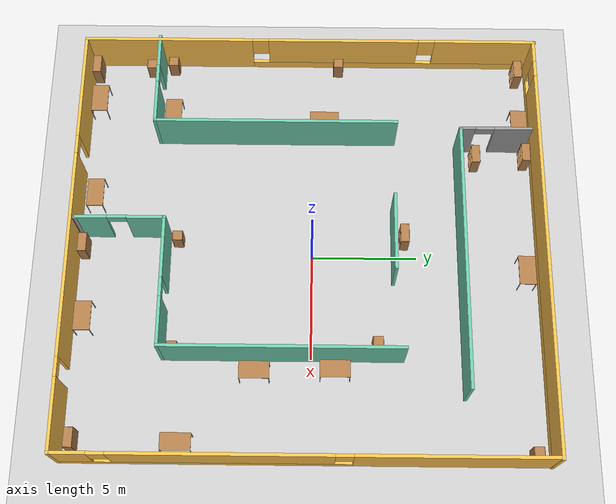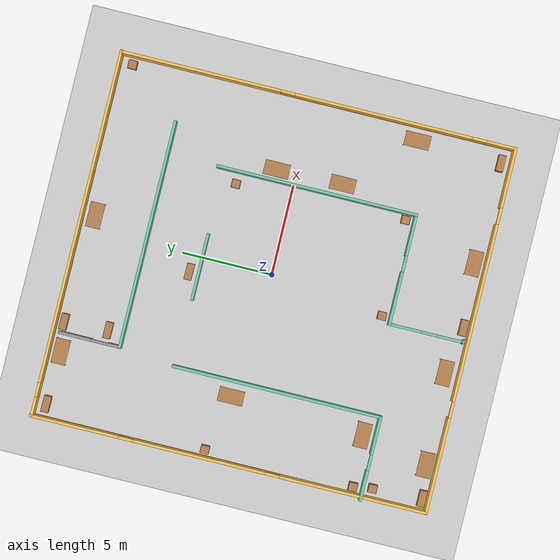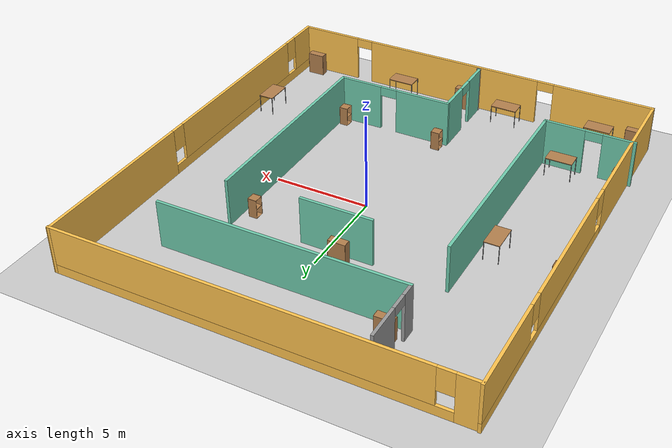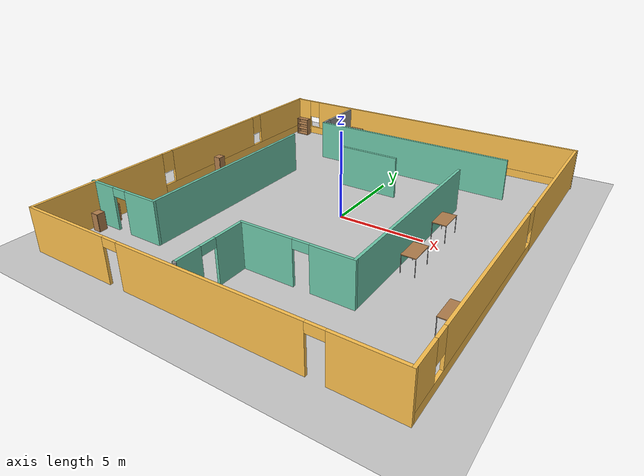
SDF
<sdf version="1.6">
 <world name="default">
  <light name="sun" type="directional">
   <pose>0 0 10 0 -0 0</pose>
   <diffuse>0.8 0.8 0.8 1</diffuse>
   <specular>0.1 0.1 0.1 1</specular>
   <attenuation>
    <range>1000</range>
    <constant>0.9</constant>
    <linear>0.01</linear>
    <quadratic>0.001</quadratic>
   </attenuation>
   <direction>-0.5 0.5 -1</direction>
  </light>
  <model name="ground_plane">
   <static>1</static>
   <link name="link">
    <collision name="collision">
     <geometry><plane><normal>0 0 1</normal><size>100 100</size></plane></geometry>
     <surface><friction><ode><mu>100</mu><mu2>50</mu2></ode></friction></surface>
    </collision>
    <visual name="visual">
     <cast_shadows>0</cast_shadows>
     <geometry><plane><normal>0 0 1</normal><size>100 100</size></plane></geometry>
     <material>
      <script><uri>file://media/materials/scripts/gazebo.material</uri><name>Gazebo/Grey</name></script>
     </material>
    </visual>
   </link>
  </model>
  <gravity>0 0 -9.8</gravity>
  <magnetic_field>6e-06 2.3e-05 -4.2e-05</magnetic_field>
  <atmosphere type="adiabatic"/>
  <physics name="default_physics" default="0" type="ode">
   <max_step_size>0.001</max_step_size>
   <real_time_factor>1</real_time_factor>
   <real_time_update_rate>1000</real_time_update_rate>
  </physics>
  <scene><ambient>0.4 0.4 0.4 1</ambient><background>0.7 0.7 0.7 1</background><shadows>1</shadows></scene>
  <spherical_coordinates>
   <surface_model>EARTH_WGS84</surface_model>
   <latitude_deg>0</latitude_deg>
   <longitude_deg>0</longitude_deg>
   <elevation>0</elevation>
   <heading_deg>0</heading_deg>
  </spherical_coordinates>
  <model name="office_pnd">
   <pose>-0.445996 -0.179176 0 0 -0 0</pose>
   <link name="Wall_16">
    <pose>0.097541 11.0012 0 0 -0 0</pose>
    <visual name="Wall_16_Visual_0">
     <pose>-9.70034 0 1.25 0 -0 0</pose>
     <geometry><box><size>1.09931 0.15 2.5</size></box></geometry>
     <material>
      <script><uri>file://media/materials/scripts/gazebo.material</uri><name>Gazebo/Grey</name></script>
      <ambient>1 0.764706 0.305882 1</ambient>
     </material>
    </visual>
    <collision name="Wall_16_Collision_0">
     <geometry><box><size>1.09931 0.15 2.5</size></box></geometry>
     <pose>-9.70034 0 1.25 0 -0 0</pose>
    </collision>
    <visual name="Wall_16_Visual_1">
     <pose>0.549656 0 0.25 0 -0 0</pose>
     <geometry><box><size>19.4007 0.15 0.5</size></box></geometry>
     <material>
      <script><uri>file://media/materials/scripts/gazebo.material</uri><name>Gazebo/Grey</name></script>
      <ambient>1 0.764706 0.305882 1</ambient>
     </material>
    </visual>
    <collision name="Wall_16_Collision_1">
     <geometry><box><size>19.4007 0.15 0.5</size></box></geometry>
     <pose>0.549656 0 0.25 0 -0 0</pose>
    </collision>
    <visual name="Wall_16_Visual_2">
     <pose>0.949656 0 1.5 0 -0 0</pose>
     <geometry><box><size>18.6007 0.15 2</size></box></geometry>
     <material>
      <script><uri>file://media/materials/scripts/gazebo.material</uri><name>Gazebo/Grey</name></script>
      <ambient>1 0.764706 0.305882 1</ambient>
     </material>
    </visual>
    <collision name="Wall_16_Collision_2">
     <geometry><box><size>18.6007 0.15 2</size></box></geometry>
     <pose>0.949656 0 1.5 0 -0 0</pose>
    </collision>
    <visual name="Wall_16_Visual_3">
     <pose>-8.75069 0 1.9 0 -0 0</pose>
     <geometry><box><size>0.8 0.15 1.2</size></box></geometry>
     <material>
      <script><uri>file://media/materials/scripts/gazebo.material</uri><name>Gazebo/Grey</name></script>
      <ambient>1 0.764706 0.305882 1</ambient>
     </material>
    </visual>
    <collision name="Wall_16_Collision_3">
     <geometry><box><size>0.8 0.15 1.2</size></box></geometry>
     <pose>-8.75069 0 1.9 0 -0 0</pose>
    </collision>
   </link>
   <link name="Wall_17">
    <pose>10.2323 -0.024395 0 0 0 -1.5708</pose>
    <visual name="Wall_17_Visual_0">
     <pose>-6.60362 0 1.25 0 -0 0</pose>
     <geometry><box><size>8.99404 0.15 2.5</size></box></geometry>
     <material>
      <script><uri>file://media/materials/scripts/gazebo.material</uri><name>Gazebo/Grey</name></script>
      <ambient>1 0.764706 0.305882 1</ambient>
     </material>
    </visual>
    <collision name="Wall_17_Collision_0">
     <geometry><box><size>8.99404 0.15 2.5</size></box></geometry>
     <pose>-6.60362 0 1.25 0 -0 0</pose>
    </collision>
    <visual name="Wall_17_Visual_1">
     <pose>4.49702 0 0.25 0 -0 0</pose>
     <geometry><box><size>13.2072 0.15 0.5</size></box></geometry>
     <material>
      <script><uri>file://media/materials/scripts/gazebo.material</uri><name>Gazebo/Grey</name></script>
      <ambient>1 0.764706 0.305882 1</ambient>
     </material>
    </visual>
    <collision name="Wall_17_Collision_1">
     <geometry><box><size>13.2072 0.15 0.5</size></box></geometry>
     <pose>4.49702 0 0.25 0 -0 0</pose>
    </collision>
    <visual name="Wall_17_Visual_2">
     <pose>3.64361 0 1.5 0 -0 0</pose>
     <geometry><box><size>9.90042 0.15 2</size></box></geometry>
     <material>
      <script><uri>file://media/materials/scripts/gazebo.material</uri><name>Gazebo/Grey</name></script>
      <ambient>1 0.764706 0.305882 1</ambient>
     </material>
    </visual>
    <collision name="Wall_17_Collision_2">
     <geometry><box><size>9.90042 0.15 2</size></box></geometry>
     <pose>3.64361 0 1.5 0 -0 0</pose>
    </collision>
    <visual name="Wall_17_Visual_3">
     <pose>10.2472 0 1.5 0 -0 0</pose>
     <geometry><box><size>1.70682 0.15 2</size></box></geometry>
     <material>
      <script><uri>file://media/materials/scripts/gazebo.material</uri><name>Gazebo/Grey</name></script>
      <ambient>1 0.764706 0.305882 1</ambient>
     </material>
    </visual>
    <collision name="Wall_17_Collision_3">
     <geometry><box><size>1.70682 0.15 2</size></box></geometry>
     <pose>10.2472 0 1.5 0 -0 0</pose>
    </collision>
    <visual name="Wall_17_Visual_4">
     <pose>-1.7066 0 1.9 0 -0 0</pose>
     <geometry><box><size>0.8 0.15 1.2</size></box></geometry>
     <material>
      <script><uri>file://media/materials/scripts/gazebo.material</uri><name>Gazebo/Grey</name></script>
      <ambient>1 0.764706 0.305882 1</ambient>
     </material>
    </visual>
    <collision name="Wall_17_Collision_4">
     <geometry><box><size>0.8 0.15 1.2</size></box></geometry>
     <pose>-1.7066 0 1.9 0 -0 0</pose>
    </collision>
    <visual name="Wall_17_Visual_5">
     <pose>8.99382 0 1.9 0 -0 0</pose>
     <geometry><box><size>0.8 0.15 1.2</size></box></geometry>
     <material>
      <script><uri>file://media/materials/scripts/gazebo.material</uri><name>Gazebo/Grey</name></script>
      <ambient>1 0.764706 0.305882 1</ambient>
     </material>
    </visual>
    <collision name="Wall_17_Collision_5">
     <geometry><box><size>0.8 0.15 1.2</size></box></geometry>
     <pose>8.99382 0 1.9 0 -0 0</pose>
    </collision>
   </link>
   <link name="Wall_18">
    <pose>0.057314 -11.05 0 0 -0 3.14159</pose>
    <visual name="Wall_18_Visual_0">
     <pose>-8.55747 0 1.25 0 -0 0</pose>
     <geometry><box><size>3.38505 0.15 2.5</size></box></geometry>
     <material>
      <script><uri>file://media/materials/scripts/gazebo.material</uri><name>Gazebo/Grey</name></script>
      <ambient>1 0.764706 0.305882 1</ambient>
     </material>
    </visual>
    <collision name="Wall_18_Collision_0">
     <geometry><box><size>3.38505 0.15 2.5</size></box></geometry>
     <pose>-8.55747 0 1.25 0 -0 0</pose>
    </collision>
    <visual name="Wall_18_Visual_1">
     <pose>-1.00439 0 1.25 0 -0 0</pose>
     <geometry><box><size>9.9211 0.15 2.5</size></box></geometry>
     <material>
      <script><uri>file://media/materials/scripts/gazebo.material</uri><name>Gazebo/Grey</name></script>
      <ambient>1 0.764706 0.305882 1</ambient>
     </material>
    </visual>
    <collision name="Wall_18_Collision_1">
     <geometry><box><size>9.9211 0.15 2.5</size></box></geometry>
     <pose>-1.00439 0 1.25 0 -0 0</pose>
    </collision>
    <visual name="Wall_18_Visual_2">
     <pose>7.55308 0 1.25 0 -0 0</pose>
     <geometry><box><size>5.39384 0.15 2.5</size></box></geometry>
     <material>
      <script><uri>file://media/materials/scripts/gazebo.material</uri><name>Gazebo/Grey</name></script>
      <ambient>1 0.764706 0.305882 1</ambient>
     </material>
    </visual>
    <collision name="Wall_18_Collision_2">
     <geometry><box><size>5.39384 0.15 2.5</size></box></geometry>
     <pose>7.55308 0 1.25 0 -0 0</pose>
    </collision>
    <visual name="Wall_18_Visual_3">
     <pose>-6.41495 0 2.25 0 -0 0</pose>
     <geometry><box><size>0.9 0.15 0.5</size></box></geometry>
     <material>
      <script><uri>file://media/materials/scripts/gazebo.material</uri><name>Gazebo/Grey</name></script>
      <ambient>1 0.764706 0.305882 1</ambient>
     </material>
    </visual>
    <collision name="Wall_18_Collision_3">
     <geometry><box><size>0.9 0.15 0.5</size></box></geometry>
     <pose>-6.41495 0 2.25 0 -0 0</pose>
    </collision>
    <visual name="Wall_18_Visual_4">
     <pose>4.40616 0 2.25 0 -0 0</pose>
     <geometry><box><size>0.9 0.15 0.5</size></box></geometry>
     <material>
      <script><uri>file://media/materials/scripts/gazebo.material</uri><name>Gazebo/Grey</name></script>
      <ambient>1 0.764706 0.305882 1</ambient>
     </material>
    </visual>
    <collision name="Wall_18_Collision_4">
     <geometry><box><size>0.9 0.15 0.5</size></box></geometry>
     <pose>4.40616 0 2.25 0 -0 0</pose>
    </collision>
   </link>
   <link name="Wall_19">
    <pose>-10.1177 3.7e-05 0 0 -0 1.5708</pose>
    <visual name="Wall_19_Visual_0">
     <pose>-6.99312 0 1.25 0 -0 0</pose>
     <geometry><box><size>8.26377 0.15 2.5</size></box></geometry>
     <material>
      <script><uri>file://media/materials/scripts/gazebo.material</uri><name>Gazebo/Grey</name></script>
      <ambient>1 0.764706 0.305882 1</ambient>
     </material>
    </visual>
    <collision name="Wall_19_Collision_0">
     <geometry><box><size>8.26377 0.15 2.5</size></box></geometry>
     <pose>-6.99312 0 1.25 0 -0 0</pose>
    </collision>
    <visual name="Wall_19_Visual_1">
     <pose>4.13188 0 0.25 0 -0 0</pose>
     <geometry><box><size>13.9862 0.15 0.5</size></box></geometry>
     <material>
      <script><uri>file://media/materials/scripts/gazebo.material</uri><name>Gazebo/Grey</name></script>
      <ambient>1 0.764706 0.305882 1</ambient>
     </material>
    </visual>
    <collision name="Wall_19_Collision_1">
     <geometry><box><size>13.9862 0.15 0.5</size></box></geometry>
     <pose>4.13188 0 0.25 0 -0 0</pose>
    </collision>
    <visual name="Wall_19_Visual_2">
     <pose>1.64194 0 1.5 0 -0 0</pose>
     <geometry><box><size>7.40634 0.15 2</size></box></geometry>
     <material>
      <script><uri>file://media/materials/scripts/gazebo.material</uri><name>Gazebo/Grey</name></script>
      <ambient>1 0.764706 0.305882 1</ambient>
     </material>
    </visual>
    <collision name="Wall_19_Collision_2">
     <geometry><box><size>7.40634 0.15 2</size></box></geometry>
     <pose>1.64194 0 1.5 0 -0 0</pose>
    </collision>
    <visual name="Wall_19_Visual_3">
     <pose>8.63505 0 1.5 0 -0 0</pose>
     <geometry><box><size>4.97989 0.15 2</size></box></geometry>
     <material>
      <script><uri>file://media/materials/scripts/gazebo.material</uri><name>Gazebo/Grey</name></script>
      <ambient>1 0.764706 0.305882 1</ambient>
     </material>
    </visual>
    <collision name="Wall_19_Collision_3">
     <geometry><box><size>4.97989 0.15 2</size></box></geometry>
     <pose>8.63505 0 1.5 0 -0 0</pose>
    </collision>
    <visual name="Wall_19_Visual_4">
     <pose>-2.46123 0 1.9 0 -0 0</pose>
     <geometry><box><size>0.8 0.15 1.2</size></box></geometry>
     <material>
      <script><uri>file://media/materials/scripts/gazebo.material</uri><name>Gazebo/Grey</name></script>
      <ambient>1 0.764706 0.305882 1</ambient>
     </material>
    </visual>
    <collision name="Wall_19_Collision_4">
     <geometry><box><size>0.8 0.15 1.2</size></box></geometry>
     <pose>-2.46123 0 1.9 0 -0 0</pose>
    </collision>
    <visual name="Wall_19_Visual_5">
     <pose>5.74511 0 1.9 0 -0 0</pose>
     <geometry><box><size>0.8 0.15 1.2</size></box></geometry>
     <material>
      <script><uri>file://media/materials/scripts/gazebo.material</uri><name>Gazebo/Grey</name></script>
      <ambient>1 0.764706 0.305882 1</ambient>
     </material>
    </visual>
    <collision name="Wall_19_Collision_5">
     <geometry><box><size>0.8 0.15 1.2</size></box></geometry>
     <pose>5.74511 0 1.9 0 -0 0</pose>
    </collision>
   </link>
   <link name="Wall_21">
    <collision name="Wall_21_Collision">
     <geometry><box><size>11.75 0.15 2.5</size></box></geometry>
     <pose>0 0 1.25 0 -0 0</pose>
    </collision>
    <visual name="Wall_21_Visual">
     <pose>0 0 1.25 0 -0 0</pose>
     <geometry><box><size>11.75 0.15 2.5</size></box></geometry>
     <material>
      <script><uri>file://media/materials/scripts/gazebo.material</uri><name>Gazebo/Grey</name></script>
      <ambient>0.435294 0.796078 0.67451 1</ambient>
     </material>
    </visual>
    <pose>-5.67254 -1.62415 0 0 0 -1.5708</pose>
   </link>
   <link name="Wall_22">
    <pose>-7.97254 -7.42415 0 0 -0 3.14159</pose>
    <visual name="Wall_22_Visual_0">
     <pose>-1.29345 0 1.25 0 -0 0</pose>
     <geometry><box><size>2.16311 0.15 2.5</size></box></geometry>
     <material>
      <script><uri>file://media/materials/scripts/gazebo.material</uri><name>Gazebo/Grey</name></script>
      <ambient>0.435294 0.796078 0.67451 1</ambient>
     </material>
    </visual>
    <collision name="Wall_22_Collision_0">
     <geometry><box><size>2.16311 0.15 2.5</size></box></geometry>
     <pose>-1.29345 0 1.25 0 -0 0</pose>
    </collision>
    <visual name="Wall_22_Visual_1">
     <pose>1.53155 0 1.25 0 -0 0</pose>
     <geometry><box><size>1.68689 0.15 2.5</size></box></geometry>
     <material>
      <script><uri>file://media/materials/scripts/gazebo.material</uri><name>Gazebo/Grey</name></script>
      <ambient>0.435294 0.796078 0.67451 1</ambient>
     </material>
    </visual>
    <collision name="Wall_22_Collision_1">
     <geometry><box><size>1.68689 0.15 2.5</size></box></geometry>
     <pose>1.53155 0 1.25 0 -0 0</pose>
    </collision>
    <visual name="Wall_22_Visual_2">
     <pose>0.238108 0 2.25 0 -0 0</pose>
     <geometry><box><size>0.9 0.15 0.5</size></box></geometry>
     <material>
      <script><uri>file://media/materials/scripts/gazebo.material</uri><name>Gazebo/Grey</name></script>
      <ambient>0.435294 0.796078 0.67451 1</ambient>
     </material>
    </visual>
    <collision name="Wall_22_Collision_2">
     <geometry><box><size>0.9 0.15 0.5</size></box></geometry>
     <pose>0.238108 0 2.25 0 -0 0</pose>
    </collision>
   </link>
   <link name="Wall_24">
    <pose>-5.36664 8.9248 0 0 0 -1.5708</pose>
    <visual name="Wall_24_Visual_0">
     <pose>-0.837668 0 1.25 0 -0 0</pose>
     <geometry><box><size>1.82466 0.15 2.5</size></box></geometry>
     <material>
      <script><uri>file://media/materials/scripts/gazebo.material</uri><name>Gazebo/Grey</name></script>
      <ambient>1 1 1 1</ambient>
     </material>
    </visual>
    <collision name="Wall_24_Collision_0">
     <geometry><box><size>1.82466 0.15 2.5</size></box></geometry>
     <pose>-0.837668 0 1.25 0 -0 0</pose>
    </collision>
    <visual name="Wall_24_Visual_1">
     <pose>1.36233 0 1.25 0 -0 0</pose>
     <geometry><box><size>0.775335 0.15 2.5</size></box></geometry>
     <material>
      <script><uri>file://media/materials/scripts/gazebo.material</uri><name>Gazebo/Grey</name></script>
      <ambient>1 1 1 1</ambient>
     </material>
    </visual>
    <collision name="Wall_24_Collision_1">
     <geometry><box><size>0.775335 0.15 2.5</size></box></geometry>
     <pose>1.36233 0 1.25 0 -0 0</pose>
    </collision>
    <visual name="Wall_24_Visual_2">
     <pose>0.524665 0 2.25 0 -0 0</pose>
     <geometry><box><size>0.9 0.15 0.5</size></box></geometry>
     <material>
      <script><uri>file://media/materials/scripts/gazebo.material</uri><name>Gazebo/Grey</name></script>
      <ambient>1 1 1 1</ambient>
     </material>
    </visual>
    <collision name="Wall_24_Collision_2">
     <geometry><box><size>0.9 0.15 0.5</size></box></geometry>
     <pose>0.524665 0 2.25 0 -0 0</pose>
    </collision>
   </link>
   <link name="Wall_25">
    <collision name="Wall_25_Collision">
     <geometry><box><size>12.75 0.15 2.5</size></box></geometry>
     <pose>0 0 1.25 0 -0 0</pose>
    </collision>
    <visual name="Wall_25_Visual">
     <pose>0 0 1.25 0 -0 0</pose>
     <geometry><box><size>12.75 0.15 2.5</size></box></geometry>
     <material>
      <script><uri>file://media/materials/scripts/gazebo.material</uri><name>Gazebo/Grey</name></script>
      <ambient>0.435294 0.796078 0.67451 1</ambient>
     </material>
    </visual>
    <pose>0.933361 7.2498 0 0 -0 0</pose>
   </link>
   <link name="Wall_28">
    <collision name="Wall_28_Collision">
     <geometry><box><size>11.25 0.15 2.5</size></box></geometry>
     <pose>0 0 1.25 0 -0 0</pose>
    </collision>
    <visual name="Wall_28_Visual">
     <pose>0 0 1.25 0 -0 0</pose>
     <geometry><box><size>11.25 0.15 2.5</size></box></geometry>
     <material>
      <script><uri>file://media/materials/scripts/gazebo.material</uri><name>Gazebo/Grey</name></script>
      <ambient>0.435294 0.796078 0.67451 1</ambient>
     </material>
    </visual>
    <pose>5.4623 -1.12943 0 0 0 -1.5708</pose>
   </link>
   <link name="Wall_29">
    <pose>2.4123 -6.67943 0 0 -0 3.14159</pose>
    <visual name="Wall_29_Visual_0">
     <pose>-1.94692 0 1.25 0 -0 0</pose>
     <geometry><box><size>2.35617 0.15 2.5</size></box></geometry>
     <material>
      <script><uri>file://media/materials/scripts/gazebo.material</uri><name>Gazebo/Grey</name></script>
      <ambient>0.435294 0.796078 0.67451 1</ambient>
     </material>
    </visual>
    <collision name="Wall_29_Collision_0">
     <geometry><box><size>2.35617 0.15 2.5</size></box></geometry>
     <pose>-1.94692 0 1.25 0 -0 0</pose>
    </collision>
    <visual name="Wall_29_Visual_1">
     <pose>1.62808 0 1.25 0 -0 0</pose>
     <geometry><box><size>2.99383 0.15 2.5</size></box></geometry>
     <material>
      <script><uri>file://media/materials/scripts/gazebo.material</uri><name>Gazebo/Grey</name></script>
      <ambient>0.435294 0.796078 0.67451 1</ambient>
     </material>
    </visual>
    <collision name="Wall_29_Collision_1">
     <geometry><box><size>2.99383 0.15 2.5</size></box></geometry>
     <pose>1.62808 0 1.25 0 -0 0</pose>
    </collision>
    <visual name="Wall_29_Visual_2">
     <pose>-0.318833 0 2.25 0 -0 0</pose>
     <geometry><box><size>0.9 0.15 0.5</size></box></geometry>
     <material>
      <script><uri>file://media/materials/scripts/gazebo.material</uri><name>Gazebo/Grey</name></script>
      <ambient>0.435294 0.796078 0.67451 1</ambient>
     </material>
    </visual>
    <collision name="Wall_29_Collision_2">
     <geometry><box><size>0.9 0.15 0.5</size></box></geometry>
     <pose>-0.318833 0 2.25 0 -0 0</pose>
    </collision>
   </link>
   <link name="Wall_30">
    <pose>-0.637698 -8.72943 0 0 0 -1.5708</pose>
    <visual name="Wall_30_Visual_0">
     <pose>-1.20345 0 1.25 0 -0 0</pose>
     <geometry><box><size>1.84311 0.15 2.5</size></box></geometry>
     <material>
      <script><uri>file://media/materials/scripts/gazebo.material</uri><name>Gazebo/Grey</name></script>
      <ambient>0.435294 0.796078 0.67451 1</ambient>
     </material>
    </visual>
    <collision name="Wall_30_Collision_0">
     <geometry><box><size>1.84311 0.15 2.5</size></box></geometry>
     <pose>-1.20345 0 1.25 0 -0 0</pose>
    </collision>
    <visual name="Wall_30_Visual_1">
     <pose>1.37156 0 1.25 0 -0 0</pose>
     <geometry><box><size>1.50689 0.15 2.5</size></box></geometry>
     <material>
      <script><uri>file://media/materials/scripts/gazebo.material</uri><name>Gazebo/Grey</name></script>
      <ambient>0.435294 0.796078 0.67451 1</ambient>
     </material>
    </visual>
    <collision name="Wall_30_Collision_1">
     <geometry><box><size>1.50689 0.15 2.5</size></box></geometry>
     <pose>1.37156 0 1.25 0 -0 0</pose>
    </collision>
    <visual name="Wall_30_Visual_2">
     <pose>0.168111 0 2.25 0 -0 0</pose>
     <geometry><box><size>0.9 0.15 0.5</size></box></geometry>
     <material>
      <script><uri>file://media/materials/scripts/gazebo.material</uri><name>Gazebo/Grey</name></script>
      <ambient>0.435294 0.796078 0.67451 1</ambient>
     </material>
    </visual>
    <collision name="Wall_30_Collision_2">
     <geometry><box><size>0.9 0.15 0.5</size></box></geometry>
     <pose>0.168111 0 2.25 0 -0 0</pose>
    </collision>
   </link>
   <link name="Wall_31">
    <collision name="Wall_31_Collision">
     <geometry><box><size>0.25 0.15 2.5</size></box></geometry>
     <pose>0 0 1.25 0 -0 0</pose>
    </collision>
    <visual name="Wall_31_Visual">
     <pose>0 0 1.25 0 -0 0</pose>
     <geometry><box><size>0.25 0.15 2.5</size></box></geometry>
     <material>
      <script><uri>file://media/materials/scripts/gazebo.material</uri><name>Gazebo/Grey</name></script>
      <ambient>1 1 1 1</ambient>
     </material>
    </visual>
    <pose>-0.602343 -10.8148 0 0 0 -0.785398</pose>
   </link>
   <link name="Wall_40">
    <collision name="Wall_40_Collision">
     <geometry><box><size>3.75 0.15 2.5</size></box></geometry>
     <pose>0 0 1.25 0 -0 0</pose>
    </collision>
    <visual name="Wall_40_Visual">
     <pose>0 0 1.25 0 -0 0</pose>
     <geometry><box><size>3.75 0.15 2.5</size></box></geometry>
     <material>
      <script><uri>file://media/materials/scripts/gazebo.material</uri><name>Gazebo/Grey</name></script>
      <ambient>0.435294 0.796078 0.67451 1</ambient>
     </material>
    </visual>
    <pose>-0.094987 4.0556 0 0 -0 0</pose>
   </link>
   <static>1</static>
  </model>
  <model name="bookshelf">
   <static>1</static>
   <link name="link">
    <inertial><mass>1</mass></inertial>
    <collision name="back">
     <pose>0 0.005 0.6 0 -0 0</pose>
     <geometry><box><size>0.9 0.01 1.2</size></box></geometry>
    </collision>
    <visual name="visual1">
     <pose>0 0.005 0.6 0 -0 0</pose>
     <geometry><box><size>0.9 0.01 1.2</size></box></geometry>
     <material>
      <script><uri>file://media/materials/scripts/gazebo.material</uri><name>Gazebo/Wood</name></script>
     </material>
    </visual>
    <collision name="left_side">
     <pose>0.45 -0.195 0.6 0 -0 0</pose>
     <geometry><box><size>0.02 0.4 1.2</size></box></geometry>
    </collision>
    <visual name="visual2">
     <pose>0.45 -0.195 0.6 0 -0 0</pose>
     <geometry><box><size>0.02 0.4 1.2</size></box></geometry>
     <material>
      <script><uri>file://media/materials/scripts/gazebo.material</uri><name>Gazebo/Wood</name></script>
     </material>
    </visual>
    <collision name="right_side">
     <pose>-0.45 -0.195 0.6 0 -0 0</pose>
     <geometry><box><size>0.02 0.4 1.2</size></box></geometry>
    </collision>
    <visual name="visual3">
     <pose>-0.45 -0.195 0.6 0 -0 0</pose>
     <geometry><box><size>0.02 0.4 1.2</size></box></geometry>
     <material>
      <script><uri>file://media/materials/scripts/gazebo.material</uri><name>Gazebo/Wood</name></script>
     </material>
    </visual>
    <collision name="bottom">
     <pose>0 -0.195 0.03 0 -0 0</pose>
     <geometry><box><size>0.88 0.4 0.06</size></box></geometry>
    </collision>
    <visual name="visual4">
     <pose>0 -0.195 0.03 0 -0 0</pose>
     <geometry><box><size>0.88 0.4 0.06</size></box></geometry>
     <material>
      <script><uri>file://media/materials/scripts/gazebo.material</uri><name>Gazebo/Wood</name></script>
     </material>
    </visual>
    <collision name="top">
     <pose>0 -0.195 1.19 0 -0 0</pose>
     <geometry><box><size>0.88 0.4 0.02</size></box></geometry>
    </collision>
    <visual name="visual5">
     <pose>0 -0.195 1.19 0 -0 0</pose>
     <geometry><box><size>0.88 0.4 0.02</size></box></geometry>
     <material>
      <script><uri>file://media/materials/scripts/gazebo.material</uri><name>Gazebo/Wood</name></script>
     </material>
    </visual>
    <collision name="low_shelf">
     <pose>0 -0.195 0.43 0 -0 0</pose>
     <geometry><box><size>0.88 0.4 0.02</size></box></geometry>
    </collision>
    <visual name="visual6">
     <pose>0 -0.195 0.43 0 -0 0</pose>
     <geometry><box><size>0.88 0.4 0.02</size></box></geometry>
     <material>
      <script><uri>file://media/materials/scripts/gazebo.material</uri><name>Gazebo/Wood</name></script>
     </material>
    </visual>
    <collision name="high_shelf">
     <pose>0 -0.195 0.8 0 -0 0</pose>
     <geometry><box><size>0.88 0.4 0.02</size></box></geometry>
    </collision>
    <visual name="visual7">
     <pose>0 -0.195 0.8 0 -0 0</pose>
     <geometry><box><size>0.88 0.4 0.02</size></box></geometry>
     <material>
      <script><uri>file://media/materials/scripts/gazebo.material</uri><name>Gazebo/Wood</name></script>
     </material>
    </visual>
   </link>
   <pose>-9.9054 -10.7111 0 0 -0 0</pose>
  </model>
  <model name="bookshelf_clone">
   <static>1</static>
   <link name="link">
    <inertial><mass>1</mass></inertial>
    <collision name="back">
     <pose>0 0.005 0.6 0 -0 0</pose>
     <geometry><box><size>0.9 0.01 1.2</size></box></geometry>
    </collision>
    <visual name="visual1">
     <pose>0 0.005 0.6 0 -0 0</pose>
     <geometry><box><size>0.9 0.01 1.2</size></box></geometry>
     <material>
      <script><uri>file://media/materials/scripts/gazebo.material</uri><name>Gazebo/Wood</name></script>
     </material>
    </visual>
    <collision name="left_side">
     <pose>0.45 -0.195 0.6 0 -0 0</pose>
     <geometry><box><size>0.02 0.4 1.2</size></box></geometry>
    </collision>
    <visual name="visual2">
     <pose>0.45 -0.195 0.6 0 -0 0</pose>
     <geometry><box><size>0.02 0.4 1.2</size></box></geometry>
     <material>
      <script><uri>file://media/materials/scripts/gazebo.material</uri><name>Gazebo/Wood</name></script>
     </material>
    </visual>
    <collision name="right_side">
     <pose>-0.45 -0.195 0.6 0 -0 0</pose>
     <geometry><box><size>0.02 0.4 1.2</size></box></geometry>
    </collision>
    <visual name="visual3">
     <pose>-0.45 -0.195 0.6 0 -0 0</pose>
     <geometry><box><size>0.02 0.4 1.2</size></box></geometry>
     <material>
      <script><uri>file://media/materials/scripts/gazebo.material</uri><name>Gazebo/Wood</name></script>
     </material>
    </visual>
    <collision name="bottom">
     <pose>0 -0.195 0.03 0 -0 0</pose>
     <geometry><box><size>0.88 0.4 0.06</size></box></geometry>
    </collision>
    <visual name="visual4">
     <pose>0 -0.195 0.03 0 -0 0</pose>
     <geometry><box><size>0.88 0.4 0.06</size></box></geometry>
     <material>
      <script><uri>file://media/materials/scripts/gazebo.material</uri><name>Gazebo/Wood</name></script>
     </material>
    </visual>
    <collision name="top">
     <pose>0 -0.195 1.19 0 -0 0</pose>
     <geometry><box><size>0.88 0.4 0.02</size></box></geometry>
    </collision>
    <visual name="visual5">
     <pose>0 -0.195 1.19 0 -0 0</pose>
     <geometry><box><size>0.88 0.4 0.02</size></box></geometry>
     <material>
      <script><uri>file://media/materials/scripts/gazebo.material</uri><name>Gazebo/Wood</name></script>
     </material>
    </visual>
    <collision name="low_shelf">
     <pose>0 -0.195 0.43 0 -0 0</pose>
     <geometry><box><size>0.88 0.4 0.02</size></box></geometry>
    </collision>
    <visual name="visual6">
     <pose>0 -0.195 0.43 0 -0 0</pose>
     <geometry><box><size>0.88 0.4 0.02</size></box></geometry>
     <material>
      <script><uri>file://media/materials/scripts/gazebo.material</uri><name>Gazebo/Wood</name></script>
     </material>
    </visual>
    <collision name="high_shelf">
     <pose>0 -0.195 0.8 0 -0 0</pose>
     <geometry><box><size>0.88 0.4 0.02</size></box></geometry>
    </collision>
    <visual name="visual7">
     <pose>0 -0.195 0.8 0 -0 0</pose>
     <geometry><box><size>0.88 0.4 0.02</size></box></geometry>
     <material>
      <script><uri>file://media/materials/scripts/gazebo.material</uri><name>Gazebo/Wood</name></script>
     </material>
    </visual>
   </link>
   <pose>-9.80392 10.4508 0 0 -0 0</pose>
  </model>
  <model name="bookshelf_clone_0">
   <static>1</static>
   <link name="link">
    <inertial><mass>1</mass></inertial>
    <collision name="back">
     <pose>0 0.005 0.6 0 -0 0</pose>
     <geometry><box><size>0.9 0.01 1.2</size></box></geometry>
    </collision>
    <visual name="visual1">
     <pose>0 0.005 0.6 0 -0 0</pose>
     <geometry><box><size>0.9 0.01 1.2</size></box></geometry>
     <material>
      <script><uri>file://media/materials/scripts/gazebo.material</uri><name>Gazebo/Wood</name></script>
     </material>
    </visual>
    <collision name="left_side">
     <pose>0.45 -0.195 0.6 0 -0 0</pose>
     <geometry><box><size>0.02 0.4 1.2</size></box></geometry>
    </collision>
    <visual name="visual2">
     <pose>0.45 -0.195 0.6 0 -0 0</pose>
     <geometry><box><size>0.02 0.4 1.2</size></box></geometry>
     <material>
      <script><uri>file://media/materials/scripts/gazebo.material</uri><name>Gazebo/Wood</name></script>
     </material>
    </visual>
    <collision name="right_side">
     <pose>-0.45 -0.195 0.6 0 -0 0</pose>
     <geometry><box><size>0.02 0.4 1.2</size></box></geometry>
    </collision>
    <visual name="visual3">
     <pose>-0.45 -0.195 0.6 0 -0 0</pose>
     <geometry><box><size>0.02 0.4 1.2</size></box></geometry>
     <material>
      <script><uri>file://media/materials/scripts/gazebo.material</uri><name>Gazebo/Wood</name></script>
     </material>
    </visual>
    <collision name="bottom">
     <pose>0 -0.195 0.03 0 -0 0</pose>
     <geometry><box><size>0.88 0.4 0.06</size></box></geometry>
    </collision>
    <visual name="visual4">
     <pose>0 -0.195 0.03 0 -0 0</pose>
     <geometry><box><size>0.88 0.4 0.06</size></box></geometry>
     <material>
      <script><uri>file://media/materials/scripts/gazebo.material</uri><name>Gazebo/Wood</name></script>
     </material>
    </visual>
    <collision name="top">
     <pose>0 -0.195 1.19 0 -0 0</pose>
     <geometry><box><size>0.88 0.4 0.02</size></box></geometry>
    </collision>
    <visual name="visual5">
     <pose>0 -0.195 1.19 0 -0 0</pose>
     <geometry><box><size>0.88 0.4 0.02</size></box></geometry>
     <material>
      <script><uri>file://media/materials/scripts/gazebo.material</uri><name>Gazebo/Wood</name></script>
     </material>
    </visual>
    <collision name="low_shelf">
     <pose>0 -0.195 0.43 0 -0 0</pose>
     <geometry><box><size>0.88 0.4 0.02</size></box></geometry>
    </collision>
    <visual name="visual6">
     <pose>0 -0.195 0.43 0 -0 0</pose>
     <geometry><box><size>0.88 0.4 0.02</size></box></geometry>
     <material>
      <script><uri>file://media/materials/scripts/gazebo.material</uri><name>Gazebo/Wood</name></script>
     </material>
    </visual>
    <collision name="high_shelf">
     <pose>0 -0.195 0.8 0 -0 0</pose>
     <geometry><box><size>0.88 0.4 0.02</size></box></geometry>
    </collision>
    <visual name="visual7">
     <pose>0 -0.195 0.8 0 -0 0</pose>
     <geometry><box><size>0.88 0.4 0.02</size></box></geometry>
     <material>
      <script><uri>file://media/materials/scripts/gazebo.material</uri><name>Gazebo/Wood</name></script>
     </material>
    </visual>
   </link>
   <pose>-5.09047 8.13769 0 0 -0 0</pose>
  </model>
  <model name="bookshelf_clone_1">
   <static>1</static>
   <link name="link">
    <inertial><mass>1</mass></inertial>
    <collision name="back">
     <pose>0 0.005 0.6 0 -0 0</pose>
     <geometry><box><size>0.9 0.01 1.2</size></box></geometry>
    </collision>
    <visual name="visual1">
     <pose>0 0.005 0.6 0 -0 0</pose>
     <geometry><box><size>0.9 0.01 1.2</size></box></geometry>
     <material>
      <script><uri>file://media/materials/scripts/gazebo.material</uri><name>Gazebo/Wood</name></script>
     </material>
    </visual>
    <collision name="left_side">
     <pose>0.45 -0.195 0.6 0 -0 0</pose>
     <geometry><box><size>0.02 0.4 1.2</size></box></geometry>
    </collision>
    <visual name="visual2">
     <pose>0.45 -0.195 0.6 0 -0 0</pose>
     <geometry><box><size>0.02 0.4 1.2</size></box></geometry>
     <material>
      <script><uri>file://media/materials/scripts/gazebo.material</uri><name>Gazebo/Wood</name></script>
     </material>
    </visual>
    <collision name="right_side">
     <pose>-0.45 -0.195 0.6 0 -0 0</pose>
     <geometry><box><size>0.02 0.4 1.2</size></box></geometry>
    </collision>
    <visual name="visual3">
     <pose>-0.45 -0.195 0.6 0 -0 0</pose>
     <geometry><box><size>0.02 0.4 1.2</size></box></geometry>
     <material>
      <script><uri>file://media/materials/scripts/gazebo.material</uri><name>Gazebo/Wood</name></script>
     </material>
    </visual>
    <collision name="bottom">
     <pose>0 -0.195 0.03 0 -0 0</pose>
     <geometry><box><size>0.88 0.4 0.06</size></box></geometry>
    </collision>
    <visual name="visual4">
     <pose>0 -0.195 0.03 0 -0 0</pose>
     <geometry><box><size>0.88 0.4 0.06</size></box></geometry>
     <material>
      <script><uri>file://media/materials/scripts/gazebo.material</uri><name>Gazebo/Wood</name></script>
     </material>
    </visual>
    <collision name="top">
     <pose>0 -0.195 1.19 0 -0 0</pose>
     <geometry><box><size>0.88 0.4 0.02</size></box></geometry>
    </collision>
    <visual name="visual5">
     <pose>0 -0.195 1.19 0 -0 0</pose>
     <geometry><box><size>0.88 0.4 0.02</size></box></geometry>
     <material>
      <script><uri>file://media/materials/scripts/gazebo.material</uri><name>Gazebo/Wood</name></script>
     </material>
    </visual>
    <collision name="low_shelf">
     <pose>0 -0.195 0.43 0 -0 0</pose>
     <geometry><box><size>0.88 0.4 0.02</size></box></geometry>
    </collision>
    <visual name="visual6">
     <pose>0 -0.195 0.43 0 -0 0</pose>
     <geometry><box><size>0.88 0.4 0.02</size></box></geometry>
     <material>
      <script><uri>file://media/materials/scripts/gazebo.material</uri><name>Gazebo/Wood</name></script>
     </material>
    </visual>
    <collision name="high_shelf">
     <pose>0 -0.195 0.8 0 -0 0</pose>
     <geometry><box><size>0.88 0.4 0.02</size></box></geometry>
    </collision>
    <visual name="visual7">
     <pose>0 -0.195 0.8 0 -0 0</pose>
     <geometry><box><size>0.88 0.4 0.02</size></box></geometry>
     <material>
      <script><uri>file://media/materials/scripts/gazebo.material</uri><name>Gazebo/Wood</name></script>
     </material>
    </visual>
   </link>
   <pose>-5.20737 10.5889 0 0 -0 0</pose>
  </model>
  <model name="bookshelf_clone_2">
   <static>1</static>
   <link name="link">
    <inertial><mass>1</mass></inertial>
    <collision name="back">
     <pose>0 0.005 0.6 0 -0 0</pose>
     <geometry><box><size>0.9 0.01 1.2</size></box></geometry>
    </collision>
    <visual name="visual1">
     <pose>0 0.005 0.6 0 -0 0</pose>
     <geometry><box><size>0.9 0.01 1.2</size></box></geometry>
     <material>
      <script><uri>file://media/materials/scripts/gazebo.material</uri><name>Gazebo/Wood</name></script>
     </material>
    </visual>
    <collision name="left_side">
     <pose>0.45 -0.195 0.6 0 -0 0</pose>
     <geometry><box><size>0.02 0.4 1.2</size></box></geometry>
    </collision>
    <visual name="visual2">
     <pose>0.45 -0.195 0.6 0 -0 0</pose>
     <geometry><box><size>0.02 0.4 1.2</size></box></geometry>
     <material>
      <script><uri>file://media/materials/scripts/gazebo.material</uri><name>Gazebo/Wood</name></script>
     </material>
    </visual>
    <collision name="right_side">
     <pose>-0.45 -0.195 0.6 0 -0 0</pose>
     <geometry><box><size>0.02 0.4 1.2</size></box></geometry>
    </collision>
    <visual name="visual3">
     <pose>-0.45 -0.195 0.6 0 -0 0</pose>
     <geometry><box><size>0.02 0.4 1.2</size></box></geometry>
     <material>
      <script><uri>file://media/materials/scripts/gazebo.material</uri><name>Gazebo/Wood</name></script>
     </material>
    </visual>
    <collision name="bottom">
     <pose>0 -0.195 0.03 0 -0 0</pose>
     <geometry><box><size>0.88 0.4 0.06</size></box></geometry>
    </collision>
    <visual name="visual4">
     <pose>0 -0.195 0.03 0 -0 0</pose>
     <geometry><box><size>0.88 0.4 0.06</size></box></geometry>
     <material>
      <script><uri>file://media/materials/scripts/gazebo.material</uri><name>Gazebo/Wood</name></script>
     </material>
    </visual>
    <collision name="top">
     <pose>0 -0.195 1.19 0 -0 0</pose>
     <geometry><box><size>0.88 0.4 0.02</size></box></geometry>
    </collision>
    <visual name="visual5">
     <pose>0 -0.195 1.19 0 -0 0</pose>
     <geometry><box><size>0.88 0.4 0.02</size></box></geometry>
     <material>
      <script><uri>file://media/materials/scripts/gazebo.material</uri><name>Gazebo/Wood</name></script>
     </material>
    </visual>
    <collision name="low_shelf">
     <pose>0 -0.195 0.43 0 -0 0</pose>
     <geometry><box><size>0.88 0.4 0.02</size></box></geometry>
    </collision>
    <visual name="visual6">
     <pose>0 -0.195 0.43 0 -0 0</pose>
     <geometry><box><size>0.88 0.4 0.02</size></box></geometry>
     <material>
      <script><uri>file://media/materials/scripts/gazebo.material</uri><name>Gazebo/Wood</name></script>
     </material>
    </visual>
    <collision name="high_shelf">
     <pose>0 -0.195 0.8 0 -0 0</pose>
     <geometry><box><size>0.88 0.4 0.02</size></box></geometry>
    </collision>
    <visual name="visual7">
     <pose>0 -0.195 0.8 0 -0 0</pose>
     <geometry><box><size>0.88 0.4 0.02</size></box></geometry>
     <material>
      <script><uri>file://media/materials/scripts/gazebo.material</uri><name>Gazebo/Wood</name></script>
     </material>
    </visual>
   </link>
   <pose>-0.920929 4.60032 0 0 -0 0</pose>
  </model>
  <model name="bookshelf_clone_3">
   <static>1</static>
   <link name="link">
    <inertial><mass>1</mass></inertial>
    <collision name="back">
     <pose>0 0.005 0.6 0 -0 0</pose>
     <geometry><box><size>0.9 0.01 1.2</size></box></geometry>
    </collision>
    <visual name="visual1">
     <pose>0 0.005 0.6 0 -0 0</pose>
     <geometry><box><size>0.9 0.01 1.2</size></box></geometry>
     <material>
      <script><uri>file://media/materials/scripts/gazebo.material</uri><name>Gazebo/Wood</name></script>
     </material>
    </visual>
    <collision name="left_side">
     <pose>0.45 -0.195 0.6 0 -0 0</pose>
     <geometry><box><size>0.02 0.4 1.2</size></box></geometry>
    </collision>
    <visual name="visual2">
     <pose>0.45 -0.195 0.6 0 -0 0</pose>
     <geometry><box><size>0.02 0.4 1.2</size></box></geometry>
     <material>
      <script><uri>file://media/materials/scripts/gazebo.material</uri><name>Gazebo/Wood</name></script>
     </material>
    </visual>
    <collision name="right_side">
     <pose>-0.45 -0.195 0.6 0 -0 0</pose>
     <geometry><box><size>0.02 0.4 1.2</size></box></geometry>
    </collision>
    <visual name="visual3">
     <pose>-0.45 -0.195 0.6 0 -0 0</pose>
     <geometry><box><size>0.02 0.4 1.2</size></box></geometry>
     <material>
      <script><uri>file://media/materials/scripts/gazebo.material</uri><name>Gazebo/Wood</name></script>
     </material>
    </visual>
    <collision name="bottom">
     <pose>0 -0.195 0.03 0 -0 0</pose>
     <geometry><box><size>0.88 0.4 0.06</size></box></geometry>
    </collision>
    <visual name="visual4">
     <pose>0 -0.195 0.03 0 -0 0</pose>
     <geometry><box><size>0.88 0.4 0.06</size></box></geometry>
     <material>
      <script><uri>file://media/materials/scripts/gazebo.material</uri><name>Gazebo/Wood</name></script>
     </material>
    </visual>
    <collision name="top">
     <pose>0 -0.195 1.19 0 -0 0</pose>
     <geometry><box><size>0.88 0.4 0.02</size></box></geometry>
    </collision>
    <visual name="visual5">
     <pose>0 -0.195 1.19 0 -0 0</pose>
     <geometry><box><size>0.88 0.4 0.02</size></box></geometry>
     <material>
      <script><uri>file://media/materials/scripts/gazebo.material</uri><name>Gazebo/Wood</name></script>
     </material>
    </visual>
    <collision name="low_shelf">
     <pose>0 -0.195 0.43 0 -0 0</pose>
     <geometry><box><size>0.88 0.4 0.02</size></box></geometry>
    </collision>
    <visual name="visual6">
     <pose>0 -0.195 0.43 0 -0 0</pose>
     <geometry><box><size>0.88 0.4 0.02</size></box></geometry>
     <material>
      <script><uri>file://media/materials/scripts/gazebo.material</uri><name>Gazebo/Wood</name></script>
     </material>
    </visual>
    <collision name="high_shelf">
     <pose>0 -0.195 0.8 0 -0 0</pose>
     <geometry><box><size>0.88 0.4 0.02</size></box></geometry>
    </collision>
    <visual name="visual7">
     <pose>0 -0.195 0.8 0 -0 0</pose>
     <geometry><box><size>0.88 0.4 0.02</size></box></geometry>
     <material>
      <script><uri>file://media/materials/scripts/gazebo.material</uri><name>Gazebo/Wood</name></script>
     </material>
    </visual>
   </link>
   <pose>-0.315247 -10.666 0 0 -0 0</pose>
  </model>
  <model name="bookshelf_clone_4">
   <static>1</static>
   <link name="link">
    <inertial><mass>1</mass></inertial>
    <collision name="back">
     <pose>0 0.005 0.6 0 -0 0</pose>
     <geometry><box><size>0.9 0.01 1.2</size></box></geometry>
    </collision>
    <visual name="visual1">
     <pose>0 0.005 0.6 0 -0 0</pose>
     <geometry><box><size>0.9 0.01 1.2</size></box></geometry>
     <material>
      <script><uri>file://media/materials/scripts/gazebo.material</uri><name>Gazebo/Wood</name></script>
     </material>
    </visual>
    <collision name="left_side">
     <pose>0.45 -0.195 0.6 0 -0 0</pose>
     <geometry><box><size>0.02 0.4 1.2</size></box></geometry>
    </collision>
    <visual name="visual2">
     <pose>0.45 -0.195 0.6 0 -0 0</pose>
     <geometry><box><size>0.02 0.4 1.2</size></box></geometry>
     <material>
      <script><uri>file://media/materials/scripts/gazebo.material</uri><name>Gazebo/Wood</name></script>
     </material>
    </visual>
    <collision name="right_side">
     <pose>-0.45 -0.195 0.6 0 -0 0</pose>
     <geometry><box><size>0.02 0.4 1.2</size></box></geometry>
    </collision>
    <visual name="visual3">
     <pose>-0.45 -0.195 0.6 0 -0 0</pose>
     <geometry><box><size>0.02 0.4 1.2</size></box></geometry>
     <material>
      <script><uri>file://media/materials/scripts/gazebo.material</uri><name>Gazebo/Wood</name></script>
     </material>
    </visual>
    <collision name="bottom">
     <pose>0 -0.195 0.03 0 -0 0</pose>
     <geometry><box><size>0.88 0.4 0.06</size></box></geometry>
    </collision>
    <visual name="visual4">
     <pose>0 -0.195 0.03 0 -0 0</pose>
     <geometry><box><size>0.88 0.4 0.06</size></box></geometry>
     <material>
      <script><uri>file://media/materials/scripts/gazebo.material</uri><name>Gazebo/Wood</name></script>
     </material>
    </visual>
    <collision name="top">
     <pose>0 -0.195 1.19 0 -0 0</pose>
     <geometry><box><size>0.88 0.4 0.02</size></box></geometry>
    </collision>
    <visual name="visual5">
     <pose>0 -0.195 1.19 0 -0 0</pose>
     <geometry><box><size>0.88 0.4 0.02</size></box></geometry>
     <material>
      <script><uri>file://media/materials/scripts/gazebo.material</uri><name>Gazebo/Wood</name></script>
     </material>
    </visual>
    <collision name="low_shelf">
     <pose>0 -0.195 0.43 0 -0 0</pose>
     <geometry><box><size>0.88 0.4 0.02</size></box></geometry>
    </collision>
    <visual name="visual6">
     <pose>0 -0.195 0.43 0 -0 0</pose>
     <geometry><box><size>0.88 0.4 0.02</size></box></geometry>
     <material>
      <script><uri>file://media/materials/scripts/gazebo.material</uri><name>Gazebo/Wood</name></script>
     </material>
    </visual>
    <collision name="high_shelf">
     <pose>0 -0.195 0.8 0 -0 0</pose>
     <geometry><box><size>0.88 0.4 0.02</size></box></geometry>
    </collision>
    <visual name="visual7">
     <pose>0 -0.195 0.8 0 -0 0</pose>
     <geometry><box><size>0.88 0.4 0.02</size></box></geometry>
     <material>
      <script><uri>file://media/materials/scripts/gazebo.material</uri><name>Gazebo/Wood</name></script>
     </material>
    </visual>
   </link>
   <pose>8.89357 -10.5027 0 0 -0 0</pose>
  </model>
  <model name="cabinet">
   <static>1</static>
   <link name="cabinet_bottom_plate">
    <inertial>
     <pose>0 0 -1 0 -0 0</pose>
     <inertia><ixx>2.05</ixx><ixy>0</ixy><ixz>0</ixz><iyy>2.05</iyy><iyz>0</iyz><izz>2.05</izz></inertia>
     <mass>25</mass>
    </inertial>
    <collision name="cabinet_bottom_plate_geom">
     <pose>0 0 0.01 0 -0 0</pose>
     <geometry><box><size>0.45 0.45 0.02</size></box></geometry>
    </collision>
    <visual name="cabinet_bottom_plate_geom_visual">
     <pose>0 0 0.01 0 -0 0</pose>
     <geometry><box><size>0.45 0.45 0.02</size></box></geometry>
     <material>
      <script><uri>file://media/materials/scripts/gazebo.material</uri><name>Gazebo/Wood</name></script>
     </material>
    </visual>
    <collision name="cabinet_bottom_plate_geom_cabinet_back_plate">
     <pose>0.235 0 0.51 0 -0 0</pose>
     <geometry><box><size>0.02 0.45 1.02</size></box></geometry>
    </collision>
    <visual name="cabinet_bottom_plate_geom_cabinet_back_plate_visual">
     <pose>0.235 0 0.51 0 -0 0</pose>
     <geometry><box><size>0.02 0.45 1.02</size></box></geometry>
     <material>
      <script><uri>file://media/materials/scripts/gazebo.material</uri><name>Gazebo/Wood</name></script>
     </material>
    </visual>
    <collision name="cabinet_bottom_plate_geom_cabinet_left_plate">
     <pose>0 0.235 0.51 0 -0 0</pose>
     <geometry><box><size>0.45 0.02 1.02</size></box></geometry>
    </collision>
    <visual name="cabinet_bottom_plate_geom_cabinet_left_plate_visual">
     <pose>0 0.235 0.51 0 -0 0</pose>
     <geometry><box><size>0.45 0.02 1.02</size></box></geometry>
     <material>
      <script><uri>file://media/materials/scripts/gazebo.material</uri><name>Gazebo/Wood</name></script>
     </material>
    </visual>
    <collision name="cabinet_bottom_plate_geom_cabinet_middle_plate">
     <pose>0 0 0.51 0 -0 0</pose>
     <geometry><box><size>0.45 0.45 0.02</size></box></geometry>
    </collision>
    <visual name="cabinet_bottom_plate_geom_cabinet_middle_plate_visual">
     <pose>0 0 0.51 0 -0 0</pose>
     <geometry><box><size>0.45 0.45 0.02</size></box></geometry>
     <material>
      <script><uri>file://media/materials/scripts/gazebo.material</uri><name>Gazebo/Wood</name></script>
     </material>
    </visual>
    <collision name="cabinet_bottom_plate_geom_cabinet_right_plate">
     <pose>0 -0.235 0.51 0 -0 0</pose>
     <geometry><box><size>0.45 0.02 1.02</size></box></geometry>
    </collision>
    <visual name="cabinet_bottom_plate_geom_cabinet_right_plate_visual">
     <pose>0 -0.235 0.51 0 -0 0</pose>
     <geometry><box><size>0.45 0.02 1.02</size></box></geometry>
     <material>
      <script><uri>file://media/materials/scripts/gazebo.material</uri><name>Gazebo/Wood</name></script>
     </material>
    </visual>
    <collision name="cabinet_bottom_plate_geom_cabinet_top_plate">
     <pose>0 0 1.01 0 -0 0</pose>
     <geometry><box><size>0.45 0.45 0.02</size></box></geometry>
    </collision>
    <visual name="cabinet_bottom_plate_geom_cabinet_top_plate_visual">
     <pose>0 0 1.01 0 -0 0</pose>
     <geometry><box><size>0.45 0.45 0.02</size></box></geometry>
     <material>
      <script><uri>file://media/materials/scripts/gazebo.material</uri><name>Gazebo/Wood</name></script>
     </material>
    </visual>
   </link>
   <pose>-10.1871 -7.08274 0 0 -0 0</pose>
  </model>
  <model name="cabinet_clone">
   <static>1</static>
   <link name="cabinet_bottom_plate">
    <inertial>
     <pose>0 0 -1 0 -0 0</pose>
     <inertia><ixx>2.05</ixx><ixy>0</ixy><ixz>0</ixz><iyy>2.05</iyy><iyz>0</iyz><izz>2.05</izz></inertia>
     <mass>25</mass>
    </inertial>
    <collision name="cabinet_bottom_plate_geom">
     <pose>0 0 0.01 0 -0 0</pose>
     <geometry><box><size>0.45 0.45 0.02</size></box></geometry>
    </collision>
    <visual name="cabinet_bottom_plate_geom_visual">
     <pose>0 0 0.01 0 -0 0</pose>
     <geometry><box><size>0.45 0.45 0.02</size></box></geometry>
     <material>
      <script><uri>file://media/materials/scripts/gazebo.material</uri><name>Gazebo/Wood</name></script>
     </material>
    </visual>
    <collision name="cabinet_bottom_plate_geom_cabinet_back_plate">
     <pose>0.235 0 0.51 0 -0 0</pose>
     <geometry><box><size>0.02 0.45 1.02</size></box></geometry>
    </collision>
    <visual name="cabinet_bottom_plate_geom_cabinet_back_plate_visual">
     <pose>0.235 0 0.51 0 -0 0</pose>
     <geometry><box><size>0.02 0.45 1.02</size></box></geometry>
     <material>
      <script><uri>file://media/materials/scripts/gazebo.material</uri><name>Gazebo/Wood</name></script>
     </material>
    </visual>
    <collision name="cabinet_bottom_plate_geom_cabinet_left_plate">
     <pose>0 0.235 0.51 0 -0 0</pose>
     <geometry><box><size>0.45 0.02 1.02</size></box></geometry>
    </collision>
    <visual name="cabinet_bottom_plate_geom_cabinet_left_plate_visual">
     <pose>0 0.235 0.51 0 -0 0</pose>
     <geometry><box><size>0.45 0.02 1.02</size></box></geometry>
     <material>
      <script><uri>file://media/materials/scripts/gazebo.material</uri><name>Gazebo/Wood</name></script>
     </material>
    </visual>
    <collision name="cabinet_bottom_plate_geom_cabinet_middle_plate">
     <pose>0 0 0.51 0 -0 0</pose>
     <geometry><box><size>0.45 0.45 0.02</size></box></geometry>
    </collision>
    <visual name="cabinet_bottom_plate_geom_cabinet_middle_plate_visual">
     <pose>0 0 0.51 0 -0 0</pose>
     <geometry><box><size>0.45 0.45 0.02</size></box></geometry>
     <material>
      <script><uri>file://media/materials/scripts/gazebo.material</uri><name>Gazebo/Wood</name></script>
     </material>
    </visual>
    <collision name="cabinet_bottom_plate_geom_cabinet_right_plate">
     <pose>0 -0.235 0.51 0 -0 0</pose>
     <geometry><box><size>0.45 0.02 1.02</size></box></geometry>
    </collision>
    <visual name="cabinet_bottom_plate_geom_cabinet_right_plate_visual">
     <pose>0 -0.235 0.51 0 -0 0</pose>
     <geometry><box><size>0.45 0.02 1.02</size></box></geometry>
     <material>
      <script><uri>file://media/materials/scripts/gazebo.material</uri><name>Gazebo/Wood</name></script>
     </material>
    </visual>
    <collision name="cabinet_bottom_plate_geom_cabinet_top_plate">
     <pose>0 0 1.01 0 -0 0</pose>
     <geometry><box><size>0.45 0.45 0.02</size></box></geometry>
    </collision>
    <visual name="cabinet_bottom_plate_geom_cabinet_top_plate_visual">
     <pose>0 0 1.01 0 -0 0</pose>
     <geometry><box><size>0.45 0.45 0.02</size></box></geometry>
     <material>
      <script><uri>file://media/materials/scripts/gazebo.material</uri><name>Gazebo/Wood</name></script>
     </material>
    </visual>
   </link>
   <pose>-10.1589 1.25126 0 0 -0 0</pose>
  </model>
  <model name="cabinet_clone_0">
   <static>1</static>
   <link name="cabinet_bottom_plate">
    <inertial>
     <pose>0 0 -1 0 -0 0</pose>
     <inertia><ixx>2.05</ixx><ixy>0</ixy><ixz>0</ixz><iyy>2.05</iyy><iyz>0</iyz><izz>2.05</izz></inertia>
     <mass>25</mass>
    </inertial>
    <collision name="cabinet_bottom_plate_geom">
     <pose>0 0 0.01 0 -0 0</pose>
     <geometry><box><size>0.45 0.45 0.02</size></box></geometry>
    </collision>
    <visual name="cabinet_bottom_plate_geom_visual">
     <pose>0 0 0.01 0 -0 0</pose>
     <geometry><box><size>0.45 0.45 0.02</size></box></geometry>
     <material>
      <script><uri>file://media/materials/scripts/gazebo.material</uri><name>Gazebo/Wood</name></script>
     </material>
    </visual>
    <collision name="cabinet_bottom_plate_geom_cabinet_back_plate">
     <pose>0.235 0 0.51 0 -0 0</pose>
     <geometry><box><size>0.02 0.45 1.02</size></box></geometry>
    </collision>
    <visual name="cabinet_bottom_plate_geom_cabinet_back_plate_visual">
     <pose>0.235 0 0.51 0 -0 0</pose>
     <geometry><box><size>0.02 0.45 1.02</size></box></geometry>
     <material>
      <script><uri>file://media/materials/scripts/gazebo.material</uri><name>Gazebo/Wood</name></script>
     </material>
    </visual>
    <collision name="cabinet_bottom_plate_geom_cabinet_left_plate">
     <pose>0 0.235 0.51 0 -0 0</pose>
     <geometry><box><size>0.45 0.02 1.02</size></box></geometry>
    </collision>
    <visual name="cabinet_bottom_plate_geom_cabinet_left_plate_visual">
     <pose>0 0.235 0.51 0 -0 0</pose>
     <geometry><box><size>0.45 0.02 1.02</size></box></geometry>
     <material>
      <script><uri>file://media/materials/scripts/gazebo.material</uri><name>Gazebo/Wood</name></script>
     </material>
    </visual>
    <collision name="cabinet_bottom_plate_geom_cabinet_middle_plate">
     <pose>0 0 0.51 0 -0 0</pose>
     <geometry><box><size>0.45 0.45 0.02</size></box></geometry>
    </collision>
    <visual name="cabinet_bottom_plate_geom_cabinet_middle_plate_visual">
     <pose>0 0 0.51 0 -0 0</pose>
     <geometry><box><size>0.45 0.45 0.02</size></box></geometry>
     <material>
      <script><uri>file://media/materials/scripts/gazebo.material</uri><name>Gazebo/Wood</name></script>
     </material>
    </visual>
    <collision name="cabinet_bottom_plate_geom_cabinet_right_plate">
     <pose>0 -0.235 0.51 0 -0 0</pose>
     <geometry><box><size>0.45 0.02 1.02</size></box></geometry>
    </collision>
    <visual name="cabinet_bottom_plate_geom_cabinet_right_plate_visual">
     <pose>0 -0.235 0.51 0 -0 0</pose>
     <geometry><box><size>0.45 0.02 1.02</size></box></geometry>
     <material>
      <script><uri>file://media/materials/scripts/gazebo.material</uri><name>Gazebo/Wood</name></script>
     </material>
    </visual>
    <collision name="cabinet_bottom_plate_geom_cabinet_top_plate">
     <pose>0 0 1.01 0 -0 0</pose>
     <geometry><box><size>0.45 0.45 0.02</size></box></geometry>
    </collision>
    <visual name="cabinet_bottom_plate_geom_cabinet_top_plate_visual">
     <pose>0 0 1.01 0 -0 0</pose>
     <geometry><box><size>0.45 0.45 0.02</size></box></geometry>
     <material>
      <script><uri>file://media/materials/scripts/gazebo.material</uri><name>Gazebo/Wood</name></script>
     </material>
    </visual>
   </link>
   <pose>4.65359 -6.39078 0 0 -0 0</pose>
  </model>
  <model name="cabinet_clone_1">
   <static>1</static>
   <link name="cabinet_bottom_plate">
    <inertial>
     <pose>0 0 -1 0 -0 0</pose>
     <inertia><ixx>2.05</ixx><ixy>0</ixy><ixz>0</ixz><iyy>2.05</iyy><iyz>0</iyz><izz>2.05</izz></inertia>
     <mass>25</mass>
    </inertial>
    <collision name="cabinet_bottom_plate_geom">
     <pose>0 0 0.01 0 -0 0</pose>
     <geometry><box><size>0.45 0.45 0.02</size></box></geometry>
    </collision>
    <visual name="cabinet_bottom_plate_geom_visual">
     <pose>0 0 0.01 0 -0 0</pose>
     <geometry><box><size>0.45 0.45 0.02</size></box></geometry>
     <material>
      <script><uri>file://media/materials/scripts/gazebo.material</uri><name>Gazebo/Wood</name></script>
     </material>
    </visual>
    <collision name="cabinet_bottom_plate_geom_cabinet_back_plate">
     <pose>0.235 0 0.51 0 -0 0</pose>
     <geometry><box><size>0.02 0.45 1.02</size></box></geometry>
    </collision>
    <visual name="cabinet_bottom_plate_geom_cabinet_back_plate_visual">
     <pose>0.235 0 0.51 0 -0 0</pose>
     <geometry><box><size>0.02 0.45 1.02</size></box></geometry>
     <material>
      <script><uri>file://media/materials/scripts/gazebo.material</uri><name>Gazebo/Wood</name></script>
     </material>
    </visual>
    <collision name="cabinet_bottom_plate_geom_cabinet_left_plate">
     <pose>0 0.235 0.51 0 -0 0</pose>
     <geometry><box><size>0.45 0.02 1.02</size></box></geometry>
    </collision>
    <visual name="cabinet_bottom_plate_geom_cabinet_left_plate_visual">
     <pose>0 0.235 0.51 0 -0 0</pose>
     <geometry><box><size>0.45 0.02 1.02</size></box></geometry>
     <material>
      <script><uri>file://media/materials/scripts/gazebo.material</uri><name>Gazebo/Wood</name></script>
     </material>
    </visual>
    <collision name="cabinet_bottom_plate_geom_cabinet_middle_plate">
     <pose>0 0 0.51 0 -0 0</pose>
     <geometry><box><size>0.45 0.45 0.02</size></box></geometry>
    </collision>
    <visual name="cabinet_bottom_plate_geom_cabinet_middle_plate_visual">
     <pose>0 0 0.51 0 -0 0</pose>
     <geometry><box><size>0.45 0.45 0.02</size></box></geometry>
     <material>
      <script><uri>file://media/materials/scripts/gazebo.material</uri><name>Gazebo/Wood</name></script>
     </material>
    </visual>
    <collision name="cabinet_bottom_plate_geom_cabinet_right_plate">
     <pose>0 -0.235 0.51 0 -0 0</pose>
     <geometry><box><size>0.45 0.02 1.02</size></box></geometry>
    </collision>
    <visual name="cabinet_bottom_plate_geom_cabinet_right_plate_visual">
     <pose>0 -0.235 0.51 0 -0 0</pose>
     <geometry><box><size>0.45 0.02 1.02</size></box></geometry>
     <material>
      <script><uri>file://media/materials/scripts/gazebo.material</uri><name>Gazebo/Wood</name></script>
     </material>
    </visual>
    <collision name="cabinet_bottom_plate_geom_cabinet_top_plate">
     <pose>0 0 1.01 0 -0 0</pose>
     <geometry><box><size>0.45 0.45 0.02</size></box></geometry>
    </collision>
    <visual name="cabinet_bottom_plate_geom_cabinet_top_plate_visual">
     <pose>0 0 1.01 0 -0 0</pose>
     <geometry><box><size>0.45 0.45 0.02</size></box></geometry>
     <material>
      <script><uri>file://media/materials/scripts/gazebo.material</uri><name>Gazebo/Wood</name></script>
     </material>
    </visual>
   </link>
   <pose>-0.749508 -6.39091 0 0 -0 0</pose>
  </model>
  <model name="cabinet_clone_3">
   <static>1</static>
   <link name="cabinet_bottom_plate">
    <inertial>
     <pose>0 0 -1 0 -0 0</pose>
     <inertia><ixx>2.05</ixx><ixy>0</ixy><ixz>0</ixz><iyy>2.05</iyy><iyz>0</iyz><izz>2.05</izz></inertia>
     <mass>25</mass>
    </inertial>
    <collision name="cabinet_bottom_plate_geom">
     <pose>0 0 0.01 0 -0 0</pose>
     <geometry><box><size>0.45 0.45 0.02</size></box></geometry>
    </collision>
    <visual name="cabinet_bottom_plate_geom_visual">
     <pose>0 0 0.01 0 -0 0</pose>
     <geometry><box><size>0.45 0.45 0.02</size></box></geometry>
     <material>
      <script><uri>file://media/materials/scripts/gazebo.material</uri><name>Gazebo/Wood</name></script>
     </material>
    </visual>
    <collision name="cabinet_bottom_plate_geom_cabinet_back_plate">
     <pose>0.235 0 0.51 0 -0 0</pose>
     <geometry><box><size>0.02 0.45 1.02</size></box></geometry>
    </collision>
    <visual name="cabinet_bottom_plate_geom_cabinet_back_plate_visual">
     <pose>0.235 0 0.51 0 -0 0</pose>
     <geometry><box><size>0.02 0.45 1.02</size></box></geometry>
     <material>
      <script><uri>file://media/materials/scripts/gazebo.material</uri><name>Gazebo/Wood</name></script>
     </material>
    </visual>
    <collision name="cabinet_bottom_plate_geom_cabinet_left_plate">
     <pose>0 0.235 0.51 0 -0 0</pose>
     <geometry><box><size>0.45 0.02 1.02</size></box></geometry>
    </collision>
    <visual name="cabinet_bottom_plate_geom_cabinet_left_plate_visual">
     <pose>0 0.235 0.51 0 -0 0</pose>
     <geometry><box><size>0.45 0.02 1.02</size></box></geometry>
     <material>
      <script><uri>file://media/materials/scripts/gazebo.material</uri><name>Gazebo/Wood</name></script>
     </material>
    </visual>
    <collision name="cabinet_bottom_plate_geom_cabinet_middle_plate">
     <pose>0 0 0.51 0 -0 0</pose>
     <geometry><box><size>0.45 0.45 0.02</size></box></geometry>
    </collision>
    <visual name="cabinet_bottom_plate_geom_cabinet_middle_plate_visual">
     <pose>0 0 0.51 0 -0 0</pose>
     <geometry><box><size>0.45 0.45 0.02</size></box></geometry>
     <material>
      <script><uri>file://media/materials/scripts/gazebo.material</uri><name>Gazebo/Wood</name></script>
     </material>
    </visual>
    <collision name="cabinet_bottom_plate_geom_cabinet_right_plate">
     <pose>0 -0.235 0.51 0 -0 0</pose>
     <geometry><box><size>0.45 0.02 1.02</size></box></geometry>
    </collision>
    <visual name="cabinet_bottom_plate_geom_cabinet_right_plate_visual">
     <pose>0 -0.235 0.51 0 -0 0</pose>
     <geometry><box><size>0.45 0.02 1.02</size></box></geometry>
     <material>
      <script><uri>file://media/materials/scripts/gazebo.material</uri><name>Gazebo/Wood</name></script>
     </material>
    </visual>
    <collision name="cabinet_bottom_plate_geom_cabinet_top_plate">
     <pose>0 0 1.01 0 -0 0</pose>
     <geometry><box><size>0.45 0.45 0.02</size></box></geometry>
    </collision>
    <visual name="cabinet_bottom_plate_geom_cabinet_top_plate_visual">
     <pose>0 0 1.01 0 -0 0</pose>
     <geometry><box><size>0.45 0.45 0.02</size></box></geometry>
     <material>
      <script><uri>file://media/materials/scripts/gazebo.material</uri><name>Gazebo/Wood</name></script>
     </material>
    </visual>
   </link>
   <pose>-10.0346 -8.15812 0 0 -0 0</pose>
  </model>
  <model name="table">
   <static>0</static>
   <link name="link">
    <collision name="surface">
     <pose>0 0 1 0 -0 0</pose>
     <geometry><box><size>1.5 0.8 0.03</size></box></geometry>
     <surface><friction><ode><mu>0.6</mu><mu2>0.6</mu2></ode></friction></surface>
    </collision>
    <visual name="visual1">
     <pose>0 0 1 0 -0 0</pose>
     <geometry><box><size>1.4 0.8 0.04</size></box></geometry>
     <material>
      <script><uri>file://media/materials/scripts/gazebo.material</uri><name>Gazebo/Wood</name></script>
     </material>
    </visual>
    <collision name="front_left_leg">
     <pose>0.68 0.38 0.5 0 -0 0</pose>
     <geometry><cylinder><radius>0.02</radius><length>1</length></cylinder></geometry>
    </collision>
    <visual name="front_left_leg">
     <pose>0.68 0.38 0.5 0 -0 0</pose>
     <geometry><cylinder><radius>0.02</radius><length>1</length></cylinder></geometry>
     <material>
      <script><uri>file://media/materials/scripts/gazebo.material</uri><name>Gazebo/Grey</name></script>
     </material>
    </visual>
    <collision name="front_right_leg">
     <pose>0.68 -0.38 0.5 0 -0 0</pose>
     <geometry><cylinder><radius>0.02</radius><length>1</length></cylinder></geometry>
    </collision>
    <visual name="front_right_leg">
     <pose>0.68 -0.38 0.5 0 -0 0</pose>
     <geometry><cylinder><radius>0.02</radius><length>1</length></cylinder></geometry>
     <material>
      <script><uri>file://media/materials/scripts/gazebo.material</uri><name>Gazebo/Grey</name></script>
     </material>
    </visual>
    <collision name="back_right_leg">
     <pose>-0.68 -0.38 0.5 0 -0 0</pose>
     <geometry><cylinder><radius>0.02</radius><length>1</length></cylinder></geometry>
    </collision>
    <visual name="back_right_leg">
     <pose>-0.68 -0.38 0.5 0 -0 0</pose>
     <geometry><cylinder><radius>0.02</radius><length>1</length></cylinder></geometry>
     <material>
      <script><uri>file://media/materials/scripts/gazebo.material</uri><name>Gazebo/Grey</name></script>
     </material>
    </visual>
    <collision name="back_left_leg">
     <pose>-0.68 0.38 0.5 0 -0 0</pose>
     <geometry><cylinder><radius>0.02</radius><length>1</length></cylinder></geometry>
    </collision>
    <visual name="back_left_leg">
     <pose>-0.68 0.38 0.5 0 -0 0</pose>
     <geometry><cylinder><radius>0.02</radius><length>1</length></cylinder></geometry>
     <material>
      <script><uri>file://media/materials/scripts/gazebo.material</uri><name>Gazebo/Grey</name></script>
     </material>
    </visual>
    <inertial>
     <inertia><ixx>1</ixx><ixy>0</ixy><ixz>0</ixz><iyy>1</iyy><iyz>0</iyz><izz>1</izz></inertia>
     <mass>1</mass>
    </inertial>
   </link>
   <pose>3.24933 -10.582 -1e-06 -2e-06 0 0</pose>
  </model>
  <model name="table_clone_0">
   <static>0</static>
   <link name="link">
    <collision name="surface">
     <pose>0 0 1 0 -0 0</pose>
     <geometry><box><size>1.5 0.8 0.03</size></box></geometry>
     <surface><friction><ode><mu>0.6</mu><mu2>0.6</mu2></ode></friction></surface>
    </collision>
    <visual name="visual1">
     <pose>0 0 1 0 -0 0</pose>
     <geometry><box><size>1.4 0.8 0.04</size></box></geometry>
     <material>
      <script><uri>file://media/materials/scripts/gazebo.material</uri><name>Gazebo/Wood</name></script>
     </material>
    </visual>
    <collision name="front_left_leg">
     <pose>0.68 0.38 0.5 0 -0 0</pose>
     <geometry><cylinder><radius>0.02</radius><length>1</length></cylinder></geometry>
    </collision>
    <visual name="front_left_leg">
     <pose>0.68 0.38 0.5 0 -0 0</pose>
     <geometry><cylinder><radius>0.02</radius><length>1</length></cylinder></geometry>
     <material>
      <script><uri>file://media/materials/scripts/gazebo.material</uri><name>Gazebo/Grey</name></script>
     </material>
    </visual>
    <collision name="front_right_leg">
     <pose>0.68 -0.38 0.5 0 -0 0</pose>
     <geometry><cylinder><radius>0.02</radius><length>1</length></cylinder></geometry>
    </collision>
    <visual name="front_right_leg">
     <pose>0.68 -0.38 0.5 0 -0 0</pose>
     <geometry><cylinder><radius>0.02</radius><length>1</length></cylinder></geometry>
     <material>
      <script><uri>file://media/materials/scripts/gazebo.material</uri><name>Gazebo/Grey</name></script>
     </material>
    </visual>
    <collision name="back_right_leg">
     <pose>-0.68 -0.38 0.5 0 -0 0</pose>
     <geometry><cylinder><radius>0.02</radius><length>1</length></cylinder></geometry>
    </collision>
    <visual name="back_right_leg">
     <pose>-0.68 -0.38 0.5 0 -0 0</pose>
     <geometry><cylinder><radius>0.02</radius><length>1</length></cylinder></geometry>
     <material>
      <script><uri>file://media/materials/scripts/gazebo.material</uri><name>Gazebo/Grey</name></script>
     </material>
    </visual>
    <collision name="back_left_leg">
     <pose>-0.68 0.38 0.5 0 -0 0</pose>
     <geometry><cylinder><radius>0.02</radius><length>1</length></cylinder></geometry>
    </collision>
    <visual name="back_left_leg">
     <pose>-0.68 0.38 0.5 0 -0 0</pose>
     <geometry><cylinder><radius>0.02</radius><length>1</length></cylinder></geometry>
     <material>
      <script><uri>file://media/materials/scripts/gazebo.material</uri><name>Gazebo/Grey</name></script>
     </material>
    </visual>
    <inertial>
     <inertia><ixx>1</ixx><ixy>0</ixy><ixz>0</ixz><iyy>1</iyy><iyz>0</iyz><izz>1</izz></inertia>
     <mass>1</mass>
    </inertial>
   </link>
   <pose>-8.06216 -10.6439 -8e-06 1e-06 -0 0</pose>
  </model>
  <model name="table_clone_1">
   <static>0</static>
   <link name="link">
    <collision name="surface">
     <pose>0 0 1 0 -0 0</pose>
     <geometry><box><size>1.5 0.8 0.03</size></box></geometry>
     <surface><friction><ode><mu>0.6</mu><mu2>0.6</mu2></ode></friction></surface>
    </collision>
    <visual name="visual1">
     <pose>0 0 1 0 -0 0</pose>
     <geometry><box><size>1.4 0.8 0.04</size></box></geometry>
     <material>
      <script><uri>file://media/materials/scripts/gazebo.material</uri><name>Gazebo/Wood</name></script>
     </material>
    </visual>
    <collision name="front_left_leg">
     <pose>0.68 0.38 0.5 0 -0 0</pose>
     <geometry><cylinder><radius>0.02</radius><length>1</length></cylinder></geometry>
    </collision>
    <visual name="front_left_leg">
     <pose>0.68 0.38 0.5 0 -0 0</pose>
     <geometry><cylinder><radius>0.02</radius><length>1</length></cylinder></geometry>
     <material>
      <script><uri>file://media/materials/scripts/gazebo.material</uri><name>Gazebo/Grey</name></script>
     </material>
    </visual>
    <collision name="front_right_leg">
     <pose>0.68 -0.38 0.5 0 -0 0</pose>
     <geometry><cylinder><radius>0.02</radius><length>1</length></cylinder></geometry>
    </collision>
    <visual name="front_right_leg">
     <pose>0.68 -0.38 0.5 0 -0 0</pose>
     <geometry><cylinder><radius>0.02</radius><length>1</length></cylinder></geometry>
     <material>
      <script><uri>file://media/materials/scripts/gazebo.material</uri><name>Gazebo/Grey</name></script>
     </material>
    </visual>
    <collision name="back_right_leg">
     <pose>-0.68 -0.38 0.5 0 -0 0</pose>
     <geometry><cylinder><radius>0.02</radius><length>1</length></cylinder></geometry>
    </collision>
    <visual name="back_right_leg">
     <pose>-0.68 -0.38 0.5 0 -0 0</pose>
     <geometry><cylinder><radius>0.02</radius><length>1</length></cylinder></geometry>
     <material>
      <script><uri>file://media/materials/scripts/gazebo.material</uri><name>Gazebo/Grey</name></script>
     </material>
    </visual>
    <collision name="back_left_leg">
     <pose>-0.68 0.38 0.5 0 -0 0</pose>
     <geometry><cylinder><radius>0.02</radius><length>1</length></cylinder></geometry>
    </collision>
    <visual name="back_left_leg">
     <pose>-0.68 0.38 0.5 0 -0 0</pose>
     <geometry><cylinder><radius>0.02</radius><length>1</length></cylinder></geometry>
     <material>
      <script><uri>file://media/materials/scripts/gazebo.material</uri><name>Gazebo/Grey</name></script>
     </material>
    </visual>
    <inertial>
     <inertia><ixx>1</ixx><ixy>0</ixy><ixz>0</ixz><iyy>1</iyy><iyz>0</iyz><izz>1</izz></inertia>
     <mass>1</mass>
    </inertial>
   </link>
   <pose>-2.9465 -10.4587 -4e-06 -2e-06 4e-06 0</pose>
  </model>
  <model name="table_clone_2">
   <static>0</static>
   <link name="link">
    <collision name="surface">
     <pose>0 0 1 0 -0 0</pose>
     <geometry><box><size>1.5 0.8 0.03</size></box></geometry>
     <surface><friction><ode><mu>0.6</mu><mu2>0.6</mu2></ode></friction></surface>
    </collision>
    <visual name="visual1">
     <pose>0 0 1 0 -0 0</pose>
     <geometry><box><size>1.4 0.8 0.04</size></box></geometry>
     <material>
      <script><uri>file://media/materials/scripts/gazebo.material</uri><name>Gazebo/Wood</name></script>
     </material>
    </visual>
    <collision name="front_left_leg">
     <pose>0.68 0.38 0.5 0 -0 0</pose>
     <geometry><cylinder><radius>0.02</radius><length>1</length></cylinder></geometry>
    </collision>
    <visual name="front_left_leg">
     <pose>0.68 0.38 0.5 0 -0 0</pose>
     <geometry><cylinder><radius>0.02</radius><length>1</length></cylinder></geometry>
     <material>
      <script><uri>file://media/materials/scripts/gazebo.material</uri><name>Gazebo/Grey</name></script>
     </material>
    </visual>
    <collision name="front_right_leg">
     <pose>0.68 -0.38 0.5 0 -0 0</pose>
     <geometry><cylinder><radius>0.02</radius><length>1</length></cylinder></geometry>
    </collision>
    <visual name="front_right_leg">
     <pose>0.68 -0.38 0.5 0 -0 0</pose>
     <geometry><cylinder><radius>0.02</radius><length>1</length></cylinder></geometry>
     <material>
      <script><uri>file://media/materials/scripts/gazebo.material</uri><name>Gazebo/Grey</name></script>
     </material>
    </visual>
    <collision name="back_right_leg">
     <pose>-0.68 -0.38 0.5 0 -0 0</pose>
     <geometry><cylinder><radius>0.02</radius><length>1</length></cylinder></geometry>
    </collision>
    <visual name="back_right_leg">
     <pose>-0.68 -0.38 0.5 0 -0 0</pose>
     <geometry><cylinder><radius>0.02</radius><length>1</length></cylinder></geometry>
     <material>
      <script><uri>file://media/materials/scripts/gazebo.material</uri><name>Gazebo/Grey</name></script>
     </material>
    </visual>
    <collision name="back_left_leg">
     <pose>-0.68 0.38 0.5 0 -0 0</pose>
     <geometry><cylinder><radius>0.02</radius><length>1</length></cylinder></geometry>
    </collision>
    <visual name="back_left_leg">
     <pose>-0.68 0.38 0.5 0 -0 0</pose>
     <geometry><cylinder><radius>0.02</radius><length>1</length></cylinder></geometry>
     <material>
      <script><uri>file://media/materials/scripts/gazebo.material</uri><name>Gazebo/Grey</name></script>
     </material>
    </visual>
    <inertial>
     <inertia><ixx>1</ixx><ixy>0</ixy><ixz>0</ixz><iyy>1</iyy><iyz>0</iyz><izz>1</izz></inertia>
     <mass>1</mass>
    </inertial>
   </link>
   <pose>-7.32263 -6.92538 -8e-06 1e-06 -0 0</pose>
  </model>
  <model name="table_clone_4">
   <static>0</static>
   <link name="link">
    <collision name="surface">
     <pose>0 0 1 0 -0 0</pose>
     <geometry><box><size>1.5 0.8 0.03</size></box></geometry>
     <surface><friction><ode><mu>0.6</mu><mu2>0.6</mu2></ode></friction></surface>
    </collision>
    <visual name="visual1">
     <pose>0 0 1 0 -0 0</pose>
     <geometry><box><size>1.4 0.8 0.04</size></box></geometry>
     <material>
      <script><uri>file://media/materials/scripts/gazebo.material</uri><name>Gazebo/Wood</name></script>
     </material>
    </visual>
    <collision name="front_left_leg">
     <pose>0.68 0.38 0.5 0 -0 0</pose>
     <geometry><cylinder><radius>0.02</radius><length>1</length></cylinder></geometry>
    </collision>
    <visual name="front_left_leg">
     <pose>0.68 0.38 0.5 0 -0 0</pose>
     <geometry><cylinder><radius>0.02</radius><length>1</length></cylinder></geometry>
     <material>
      <script><uri>file://media/materials/scripts/gazebo.material</uri><name>Gazebo/Grey</name></script>
     </material>
    </visual>
    <collision name="front_right_leg">
     <pose>0.68 -0.38 0.5 0 -0 0</pose>
     <geometry><cylinder><radius>0.02</radius><length>1</length></cylinder></geometry>
    </collision>
    <visual name="front_right_leg">
     <pose>0.68 -0.38 0.5 0 -0 0</pose>
     <geometry><cylinder><radius>0.02</radius><length>1</length></cylinder></geometry>
     <material>
      <script><uri>file://media/materials/scripts/gazebo.material</uri><name>Gazebo/Grey</name></script>
     </material>
    </visual>
    <collision name="back_right_leg">
     <pose>-0.68 -0.38 0.5 0 -0 0</pose>
     <geometry><cylinder><radius>0.02</radius><length>1</length></cylinder></geometry>
    </collision>
    <visual name="back_right_leg">
     <pose>-0.68 -0.38 0.5 0 -0 0</pose>
     <geometry><cylinder><radius>0.02</radius><length>1</length></cylinder></geometry>
     <material>
      <script><uri>file://media/materials/scripts/gazebo.material</uri><name>Gazebo/Grey</name></script>
     </material>
    </visual>
    <collision name="back_left_leg">
     <pose>-0.68 0.38 0.5 0 -0 0</pose>
     <geometry><cylinder><radius>0.02</radius><length>1</length></cylinder></geometry>
    </collision>
    <visual name="back_left_leg">
     <pose>-0.68 0.38 0.5 0 -0 0</pose>
     <geometry><cylinder><radius>0.02</radius><length>1</length></cylinder></geometry>
     <material>
      <script><uri>file://media/materials/scripts/gazebo.material</uri><name>Gazebo/Grey</name></script>
     </material>
    </visual>
    <inertial>
     <inertia><ixx>1</ixx><ixy>0</ixy><ixz>0</ixz><iyy>1</iyy><iyz>0</iyz><izz>1</izz></inertia>
     <mass>1</mass>
    </inertial>
   </link>
   <pose>0.83433 10.1227 -8e-06 1e-06 -0 0</pose>
  </model>
  <model name="table_clone_5">
   <static>0</static>
   <link name="link">
    <collision name="surface">
     <pose>0 0 1 0 -0 0</pose>
     <geometry><box><size>1.5 0.8 0.03</size></box></geometry>
     <surface><friction><ode><mu>0.6</mu><mu2>0.6</mu2></ode></friction></surface>
    </collision>
    <visual name="visual1">
     <pose>0 0 1 0 -0 0</pose>
     <geometry><box><size>1.4 0.8 0.04</size></box></geometry>
     <material>
      <script><uri>file://media/materials/scripts/gazebo.material</uri><name>Gazebo/Wood</name></script>
     </material>
    </visual>
    <collision name="front_left_leg">
     <pose>0.68 0.38 0.5 0 -0 0</pose>
     <geometry><cylinder><radius>0.02</radius><length>1</length></cylinder></geometry>
    </collision>
    <visual name="front_left_leg">
     <pose>0.68 0.38 0.5 0 -0 0</pose>
     <geometry><cylinder><radius>0.02</radius><length>1</length></cylinder></geometry>
     <material>
      <script><uri>file://media/materials/scripts/gazebo.material</uri><name>Gazebo/Grey</name></script>
     </material>
    </visual>
    <collision name="front_right_leg">
     <pose>0.68 -0.38 0.5 0 -0 0</pose>
     <geometry><cylinder><radius>0.02</radius><length>1</length></cylinder></geometry>
    </collision>
    <visual name="front_right_leg">
     <pose>0.68 -0.38 0.5 0 -0 0</pose>
     <geometry><cylinder><radius>0.02</radius><length>1</length></cylinder></geometry>
     <material>
      <script><uri>file://media/materials/scripts/gazebo.material</uri><name>Gazebo/Grey</name></script>
     </material>
    </visual>
    <collision name="back_right_leg">
     <pose>-0.68 -0.38 0.5 0 -0 0</pose>
     <geometry><cylinder><radius>0.02</radius><length>1</length></cylinder></geometry>
    </collision>
    <visual name="back_right_leg">
     <pose>-0.68 -0.38 0.5 0 -0 0</pose>
     <geometry><cylinder><radius>0.02</radius><length>1</length></cylinder></geometry>
     <material>
      <script><uri>file://media/materials/scripts/gazebo.material</uri><name>Gazebo/Grey</name></script>
     </material>
    </visual>
    <collision name="back_left_leg">
     <pose>-0.68 0.38 0.5 0 -0 0</pose>
     <geometry><cylinder><radius>0.02</radius><length>1</length></cylinder></geometry>
    </collision>
    <visual name="back_left_leg">
     <pose>-0.68 0.38 0.5 0 -0 0</pose>
     <geometry><cylinder><radius>0.02</radius><length>1</length></cylinder></geometry>
     <material>
      <script><uri>file://media/materials/scripts/gazebo.material</uri><name>Gazebo/Grey</name></script>
     </material>
    </visual>
    <inertial>
     <inertia><ixx>1</ixx><ixy>0</ixy><ixz>0</ixz><iyy>1</iyy><iyz>0</iyz><izz>1</izz></inertia>
     <mass>1</mass>
    </inertial>
   </link>
   <pose>-6.83426 10.1686 -1e-06 1e-06 -0 0</pose>
  </model>
  <model name="table_clone_7">
   <static>0</static>
   <link name="link">
    <collision name="surface">
     <pose>0 0 1 0 -0 0</pose>
     <geometry><box><size>1.5 0.8 0.03</size></box></geometry>
     <surface><friction><ode><mu>0.6</mu><mu2>0.6</mu2></ode></friction></surface>
    </collision>
    <visual name="visual1">
     <pose>0 0 1 0 -0 0</pose>
     <geometry><box><size>1.4 0.8 0.04</size></box></geometry>
     <material>
      <script><uri>file://media/materials/scripts/gazebo.material</uri><name>Gazebo/Wood</name></script>
     </material>
    </visual>
    <collision name="front_left_leg">
     <pose>0.68 0.38 0.5 0 -0 0</pose>
     <geometry><cylinder><radius>0.02</radius><length>1</length></cylinder></geometry>
    </collision>
    <visual name="front_left_leg">
     <pose>0.68 0.38 0.5 0 -0 0</pose>
     <geometry><cylinder><radius>0.02</radius><length>1</length></cylinder></geometry>
     <material>
      <script><uri>file://media/materials/scripts/gazebo.material</uri><name>Gazebo/Grey</name></script>
     </material>
    </visual>
    <collision name="front_right_leg">
     <pose>0.68 -0.38 0.5 0 -0 0</pose>
     <geometry><cylinder><radius>0.02</radius><length>1</length></cylinder></geometry>
    </collision>
    <visual name="front_right_leg">
     <pose>0.68 -0.38 0.5 0 -0 0</pose>
     <geometry><cylinder><radius>0.02</radius><length>1</length></cylinder></geometry>
     <material>
      <script><uri>file://media/materials/scripts/gazebo.material</uri><name>Gazebo/Grey</name></script>
     </material>
    </visual>
    <collision name="back_right_leg">
     <pose>-0.68 -0.38 0.5 0 -0 0</pose>
     <geometry><cylinder><radius>0.02</radius><length>1</length></cylinder></geometry>
    </collision>
    <visual name="back_right_leg">
     <pose>-0.68 -0.38 0.5 0 -0 0</pose>
     <geometry><cylinder><radius>0.02</radius><length>1</length></cylinder></geometry>
     <material>
      <script><uri>file://media/materials/scripts/gazebo.material</uri><name>Gazebo/Grey</name></script>
     </material>
    </visual>
    <collision name="back_left_leg">
     <pose>-0.68 0.38 0.5 0 -0 0</pose>
     <geometry><cylinder><radius>0.02</radius><length>1</length></cylinder></geometry>
    </collision>
    <visual name="back_left_leg">
     <pose>-0.68 0.38 0.5 0 -0 0</pose>
     <geometry><cylinder><radius>0.02</radius><length>1</length></cylinder></geometry>
     <material>
      <script><uri>file://media/materials/scripts/gazebo.material</uri><name>Gazebo/Grey</name></script>
     </material>
    </visual>
    <inertial>
     <inertia><ixx>1</ixx><ixy>0</ixy><ixz>0</ixz><iyy>1</iyy><iyz>0</iyz><izz>1</izz></inertia>
     <mass>1</mass>
    </inertial>
   </link>
   <pose>5.72968 -2.58293 -8e-06 0 0 -1.5708</pose>
  </model>
  <model name="table_clone_7_clone">
   <static>0</static>
   <link name="link">
    <collision name="surface">
     <pose>0 0 1 0 -0 0</pose>
     <geometry><box><size>1.5 0.8 0.03</size></box></geometry>
     <surface><friction><ode><mu>0.6</mu><mu2>0.6</mu2></ode></friction></surface>
    </collision>
    <visual name="visual1">
     <pose>0 0 1 0 -0 0</pose>
     <geometry><box><size>1.4 0.8 0.04</size></box></geometry>
     <material>
      <script><uri>file://media/materials/scripts/gazebo.material</uri><name>Gazebo/Wood</name></script>
     </material>
    </visual>
    <collision name="front_left_leg">
     <pose>0.68 0.38 0.5 0 -0 0</pose>
     <geometry><cylinder><radius>0.02</radius><length>1</length></cylinder></geometry>
    </collision>
    <visual name="front_left_leg">
     <pose>0.68 0.38 0.5 0 -0 0</pose>
     <geometry><cylinder><radius>0.02</radius><length>1</length></cylinder></geometry>
     <material>
      <script><uri>file://media/materials/scripts/gazebo.material</uri><name>Gazebo/Grey</name></script>
     </material>
    </visual>
    <collision name="front_right_leg">
     <pose>0.68 -0.38 0.5 0 -0 0</pose>
     <geometry><cylinder><radius>0.02</radius><length>1</length></cylinder></geometry>
    </collision>
    <visual name="front_right_leg">
     <pose>0.68 -0.38 0.5 0 -0 0</pose>
     <geometry><cylinder><radius>0.02</radius><length>1</length></cylinder></geometry>
     <material>
      <script><uri>file://media/materials/scripts/gazebo.material</uri><name>Gazebo/Grey</name></script>
     </material>
    </visual>
    <collision name="back_right_leg">
     <pose>-0.68 -0.38 0.5 0 -0 0</pose>
     <geometry><cylinder><radius>0.02</radius><length>1</length></cylinder></geometry>
    </collision>
    <visual name="back_right_leg">
     <pose>-0.68 -0.38 0.5 0 -0 0</pose>
     <geometry><cylinder><radius>0.02</radius><length>1</length></cylinder></geometry>
     <material>
      <script><uri>file://media/materials/scripts/gazebo.material</uri><name>Gazebo/Grey</name></script>
     </material>
    </visual>
    <collision name="back_left_leg">
     <pose>-0.68 0.38 0.5 0 -0 0</pose>
     <geometry><cylinder><radius>0.02</radius><length>1</length></cylinder></geometry>
    </collision>
    <visual name="back_left_leg">
     <pose>-0.68 0.38 0.5 0 -0 0</pose>
     <geometry><cylinder><radius>0.02</radius><length>1</length></cylinder></geometry>
     <material>
      <script><uri>file://media/materials/scripts/gazebo.material</uri><name>Gazebo/Grey</name></script>
     </material>
    </visual>
    <inertial>
     <inertia><ixx>1</ixx><ixy>0</ixy><ixz>0</ixz><iyy>1</iyy><iyz>0</iyz><izz>1</izz></inertia>
     <mass>1</mass>
    </inertial>
   </link>
   <pose>5.64417 1.10476 -1e-06 -1e-06 1e-06 -1.5708</pose>
  </model>
  <model name="table_clone_7_clone_0">
   <static>0</static>
   <link name="link">
    <collision name="surface">
     <pose>0 0 1 0 -0 0</pose>
     <geometry><box><size>1.5 0.8 0.03</size></box></geometry>
     <surface><friction><ode><mu>0.6</mu><mu2>0.6</mu2></ode></friction></surface>
    </collision>
    <visual name="visual1">
     <pose>0 0 1 0 -0 0</pose>
     <geometry><box><size>1.4 0.8 0.04</size></box></geometry>
     <material>
      <script><uri>file://media/materials/scripts/gazebo.material</uri><name>Gazebo/Wood</name></script>
     </material>
    </visual>
    <collision name="front_left_leg">
     <pose>0.68 0.38 0.5 0 -0 0</pose>
     <geometry><cylinder><radius>0.02</radius><length>1</length></cylinder></geometry>
    </collision>
    <visual name="front_left_leg">
     <pose>0.68 0.38 0.5 0 -0 0</pose>
     <geometry><cylinder><radius>0.02</radius><length>1</length></cylinder></geometry>
     <material>
      <script><uri>file://media/materials/scripts/gazebo.material</uri><name>Gazebo/Grey</name></script>
     </material>
    </visual>
    <collision name="front_right_leg">
     <pose>0.68 -0.38 0.5 0 -0 0</pose>
     <geometry><cylinder><radius>0.02</radius><length>1</length></cylinder></geometry>
    </collision>
    <visual name="front_right_leg">
     <pose>0.68 -0.38 0.5 0 -0 0</pose>
     <geometry><cylinder><radius>0.02</radius><length>1</length></cylinder></geometry>
     <material>
      <script><uri>file://media/materials/scripts/gazebo.material</uri><name>Gazebo/Grey</name></script>
     </material>
    </visual>
    <collision name="back_right_leg">
     <pose>-0.68 -0.38 0.5 0 -0 0</pose>
     <geometry><cylinder><radius>0.02</radius><length>1</length></cylinder></geometry>
    </collision>
    <visual name="back_right_leg">
     <pose>-0.68 -0.38 0.5 0 -0 0</pose>
     <geometry><cylinder><radius>0.02</radius><length>1</length></cylinder></geometry>
     <material>
      <script><uri>file://media/materials/scripts/gazebo.material</uri><name>Gazebo/Grey</name></script>
     </material>
    </visual>
    <collision name="back_left_leg">
     <pose>-0.68 0.38 0.5 0 -0 0</pose>
     <geometry><cylinder><radius>0.02</radius><length>1</length></cylinder></geometry>
    </collision>
    <visual name="back_left_leg">
     <pose>-0.68 0.38 0.5 0 -0 0</pose>
     <geometry><cylinder><radius>0.02</radius><length>1</length></cylinder></geometry>
     <material>
      <script><uri>file://media/materials/scripts/gazebo.material</uri><name>Gazebo/Grey</name></script>
     </material>
    </visual>
    <inertial>
     <inertia><ixx>1</ixx><ixy>0</ixy><ixz>0</ixz><iyy>1</iyy><iyz>0</iyz><izz>1</izz></inertia>
     <mass>1</mass>
    </inertial>
   </link>
   <pose>-6.98049 0.558444 -2e-06 0 1e-06 -1.5708</pose>
  </model>
  <model name="cabinet_clone_clone">
   <static>1</static>
   <link name="cabinet_bottom_plate">
    <inertial>
     <pose>0 0 -1 0 -0 0</pose>
     <inertia><ixx>2.05</ixx><ixy>0</ixy><ixz>0</ixz><iyy>2.05</iyy><iyz>0</iyz><izz>2.05</izz></inertia>
     <mass>25</mass>
    </inertial>
    <collision name="cabinet_bottom_plate_geom">
     <pose>0 0 0.01 0 -0 0</pose>
     <geometry><box><size>0.45 0.45 0.02</size></box></geometry>
    </collision>
    <visual name="cabinet_bottom_plate_geom_visual">
     <pose>0 0 0.01 0 -0 0</pose>
     <geometry><box><size>0.45 0.45 0.02</size></box></geometry>
     <material>
      <script><uri>file://media/materials/scripts/gazebo.material</uri><name>Gazebo/Wood</name></script>
     </material>
    </visual>
    <collision name="cabinet_bottom_plate_geom_cabinet_back_plate">
     <pose>0.235 0 0.51 0 -0 0</pose>
     <geometry><box><size>0.02 0.45 1.02</size></box></geometry>
    </collision>
    <visual name="cabinet_bottom_plate_geom_cabinet_back_plate_visual">
     <pose>0.235 0 0.51 0 -0 0</pose>
     <geometry><box><size>0.02 0.45 1.02</size></box></geometry>
     <material>
      <script><uri>file://media/materials/scripts/gazebo.material</uri><name>Gazebo/Wood</name></script>
     </material>
    </visual>
    <collision name="cabinet_bottom_plate_geom_cabinet_left_plate">
     <pose>0 0.235 0.51 0 -0 0</pose>
     <geometry><box><size>0.45 0.02 1.02</size></box></geometry>
    </collision>
    <visual name="cabinet_bottom_plate_geom_cabinet_left_plate_visual">
     <pose>0 0.235 0.51 0 -0 0</pose>
     <geometry><box><size>0.45 0.02 1.02</size></box></geometry>
     <material>
      <script><uri>file://media/materials/scripts/gazebo.material</uri><name>Gazebo/Wood</name></script>
     </material>
    </visual>
    <collision name="cabinet_bottom_plate_geom_cabinet_middle_plate">
     <pose>0 0 0.51 0 -0 0</pose>
     <geometry><box><size>0.45 0.45 0.02</size></box></geometry>
    </collision>
    <visual name="cabinet_bottom_plate_geom_cabinet_middle_plate_visual">
     <pose>0 0 0.51 0 -0 0</pose>
     <geometry><box><size>0.45 0.45 0.02</size></box></geometry>
     <material>
      <script><uri>file://media/materials/scripts/gazebo.material</uri><name>Gazebo/Wood</name></script>
     </material>
    </visual>
    <collision name="cabinet_bottom_plate_geom_cabinet_right_plate">
     <pose>0 -0.235 0.51 0 -0 0</pose>
     <geometry><box><size>0.45 0.02 1.02</size></box></geometry>
    </collision>
    <visual name="cabinet_bottom_plate_geom_cabinet_right_plate_visual">
     <pose>0 -0.235 0.51 0 -0 0</pose>
     <geometry><box><size>0.45 0.02 1.02</size></box></geometry>
     <material>
      <script><uri>file://media/materials/scripts/gazebo.material</uri><name>Gazebo/Wood</name></script>
     </material>
    </visual>
    <collision name="cabinet_bottom_plate_geom_cabinet_top_plate">
     <pose>0 0 1.01 0 -0 0</pose>
     <geometry><box><size>0.45 0.45 0.02</size></box></geometry>
    </collision>
    <visual name="cabinet_bottom_plate_geom_cabinet_top_plate_visual">
     <pose>0 0 1.01 0 -0 0</pose>
     <geometry><box><size>0.45 0.45 0.02</size></box></geometry>
     <material>
      <script><uri>file://media/materials/scripts/gazebo.material</uri><name>Gazebo/Wood</name></script>
     </material>
    </visual>
   </link>
   <pose>9.31281 10.1241 0 0 -0 0</pose>
  </model>
  <model name="cabinet_clone_clone_0">
   <static>1</static>
   <link name="cabinet_bottom_plate">
    <inertial>
     <pose>0 0 -1 0 -0 0</pose>
     <inertia><ixx>2.05</ixx><ixy>0</ixy><ixz>0</ixz><iyy>2.05</iyy><iyz>0</iyz><izz>2.05</izz></inertia>
     <mass>25</mass>
    </inertial>
    <collision name="cabinet_bottom_plate_geom">
     <pose>0 0 0.01 0 -0 0</pose>
     <geometry><box><size>0.45 0.45 0.02</size></box></geometry>
    </collision>
    <visual name="cabinet_bottom_plate_geom_visual">
     <pose>0 0 0.01 0 -0 0</pose>
     <geometry><box><size>0.45 0.45 0.02</size></box></geometry>
     <material>
      <script><uri>file://media/materials/scripts/gazebo.material</uri><name>Gazebo/Wood</name></script>
     </material>
    </visual>
    <collision name="cabinet_bottom_plate_geom_cabinet_back_plate">
     <pose>0.235 0 0.51 0 -0 0</pose>
     <geometry><box><size>0.02 0.45 1.02</size></box></geometry>
    </collision>
    <visual name="cabinet_bottom_plate_geom_cabinet_back_plate_visual">
     <pose>0.235 0 0.51 0 -0 0</pose>
     <geometry><box><size>0.02 0.45 1.02</size></box></geometry>
     <material>
      <script><uri>file://media/materials/scripts/gazebo.material</uri><name>Gazebo/Wood</name></script>
     </material>
    </visual>
    <collision name="cabinet_bottom_plate_geom_cabinet_left_plate">
     <pose>0 0.235 0.51 0 -0 0</pose>
     <geometry><box><size>0.45 0.02 1.02</size></box></geometry>
    </collision>
    <visual name="cabinet_bottom_plate_geom_cabinet_left_plate_visual">
     <pose>0 0.235 0.51 0 -0 0</pose>
     <geometry><box><size>0.45 0.02 1.02</size></box></geometry>
     <material>
      <script><uri>file://media/materials/scripts/gazebo.material</uri><name>Gazebo/Wood</name></script>
     </material>
    </visual>
    <collision name="cabinet_bottom_plate_geom_cabinet_middle_plate">
     <pose>0 0 0.51 0 -0 0</pose>
     <geometry><box><size>0.45 0.45 0.02</size></box></geometry>
    </collision>
    <visual name="cabinet_bottom_plate_geom_cabinet_middle_plate_visual">
     <pose>0 0 0.51 0 -0 0</pose>
     <geometry><box><size>0.45 0.45 0.02</size></box></geometry>
     <material>
      <script><uri>file://media/materials/scripts/gazebo.material</uri><name>Gazebo/Wood</name></script>
     </material>
    </visual>
    <collision name="cabinet_bottom_plate_geom_cabinet_right_plate">
     <pose>0 -0.235 0.51 0 -0 0</pose>
     <geometry><box><size>0.45 0.02 1.02</size></box></geometry>
    </collision>
    <visual name="cabinet_bottom_plate_geom_cabinet_right_plate_visual">
     <pose>0 -0.235 0.51 0 -0 0</pose>
     <geometry><box><size>0.45 0.02 1.02</size></box></geometry>
     <material>
      <script><uri>file://media/materials/scripts/gazebo.material</uri><name>Gazebo/Wood</name></script>
     </material>
    </visual>
    <collision name="cabinet_bottom_plate_geom_cabinet_top_plate">
     <pose>0 0 1.01 0 -0 0</pose>
     <geometry><box><size>0.45 0.45 0.02</size></box></geometry>
    </collision>
    <visual name="cabinet_bottom_plate_geom_cabinet_top_plate_visual">
     <pose>0 0 1.01 0 -0 0</pose>
     <geometry><box><size>0.45 0.45 0.02</size></box></geometry>
     <material>
      <script><uri>file://media/materials/scripts/gazebo.material</uri><name>Gazebo/Wood</name></script>
     </material>
    </visual>
   </link>
   <pose>4.34052 3.08784 0 0 -0 0</pose>
  </model>
  <model name="table_clone_7_clone_clone">
   <static>0</static>
   <link name="link">
    <collision name="surface">
     <pose>0 0 1 0 -0 0</pose>
     <geometry><box><size>1.5 0.8 0.03</size></box></geometry>
     <surface><friction><ode><mu>0.6</mu><mu2>0.6</mu2></ode></friction></surface>
    </collision>
    <visual name="visual1">
     <pose>0 0 1 0 -0 0</pose>
     <geometry><box><size>1.4 0.8 0.04</size></box></geometry>
     <material>
      <script><uri>file://media/materials/scripts/gazebo.material</uri><name>Gazebo/Wood</name></script>
     </material>
    </visual>
    <collision name="front_left_leg">
     <pose>0.68 0.38 0.5 0 -0 0</pose>
     <geometry><cylinder><radius>0.02</radius><length>1</length></cylinder></geometry>
    </collision>
    <visual name="front_left_leg">
     <pose>0.68 0.38 0.5 0 -0 0</pose>
     <geometry><cylinder><radius>0.02</radius><length>1</length></cylinder></geometry>
     <material>
      <script><uri>file://media/materials/scripts/gazebo.material</uri><name>Gazebo/Grey</name></script>
     </material>
    </visual>
    <collision name="front_right_leg">
     <pose>0.68 -0.38 0.5 0 -0 0</pose>
     <geometry><cylinder><radius>0.02</radius><length>1</length></cylinder></geometry>
    </collision>
    <visual name="front_right_leg">
     <pose>0.68 -0.38 0.5 0 -0 0</pose>
     <geometry><cylinder><radius>0.02</radius><length>1</length></cylinder></geometry>
     <material>
      <script><uri>file://media/materials/scripts/gazebo.material</uri><name>Gazebo/Grey</name></script>
     </material>
    </visual>
    <collision name="back_right_leg">
     <pose>-0.68 -0.38 0.5 0 -0 0</pose>
     <geometry><cylinder><radius>0.02</radius><length>1</length></cylinder></geometry>
    </collision>
    <visual name="back_right_leg">
     <pose>-0.68 -0.38 0.5 0 -0 0</pose>
     <geometry><cylinder><radius>0.02</radius><length>1</length></cylinder></geometry>
     <material>
      <script><uri>file://media/materials/scripts/gazebo.material</uri><name>Gazebo/Grey</name></script>
     </material>
    </visual>
    <collision name="back_left_leg">
     <pose>-0.68 0.38 0.5 0 -0 0</pose>
     <geometry><cylinder><radius>0.02</radius><length>1</length></cylinder></geometry>
    </collision>
    <visual name="back_left_leg">
     <pose>-0.68 0.38 0.5 0 -0 0</pose>
     <geometry><cylinder><radius>0.02</radius><length>1</length></cylinder></geometry>
     <material>
      <script><uri>file://media/materials/scripts/gazebo.material</uri><name>Gazebo/Grey</name></script>
     </material>
    </visual>
    <inertial>
     <inertia><ixx>1</ixx><ixy>0</ixy><ixz>0</ixz><iyy>1</iyy><iyz>0</iyz><izz>1</izz></inertia>
     <mass>1</mass>
    </inertial>
   </link>
   <pose>9.0144 -5.97556 -2e-06 0 0 -1.5708</pose>
  </model>
 </world>
</sdf>
